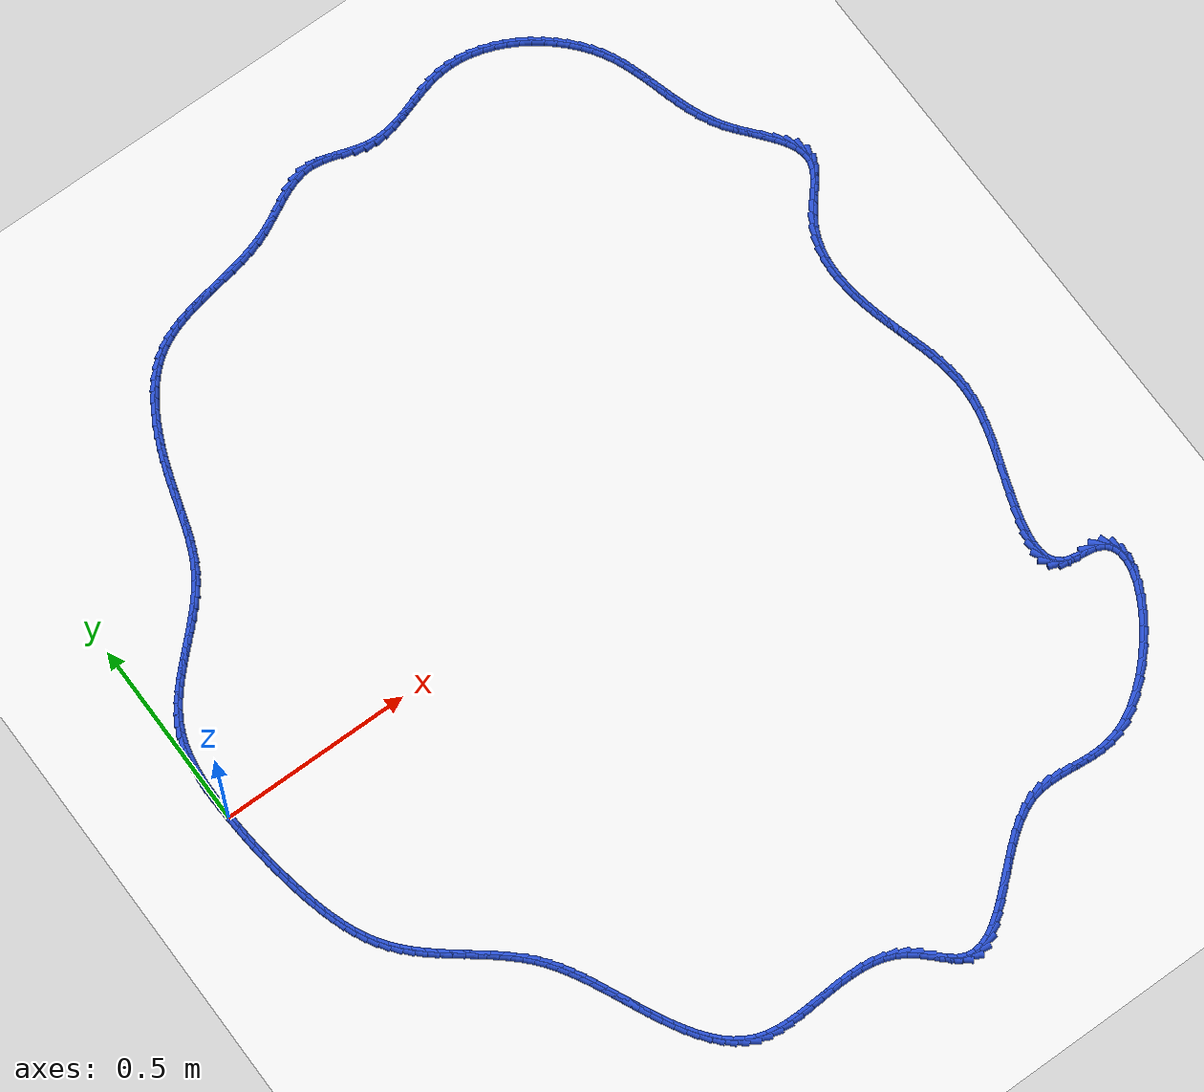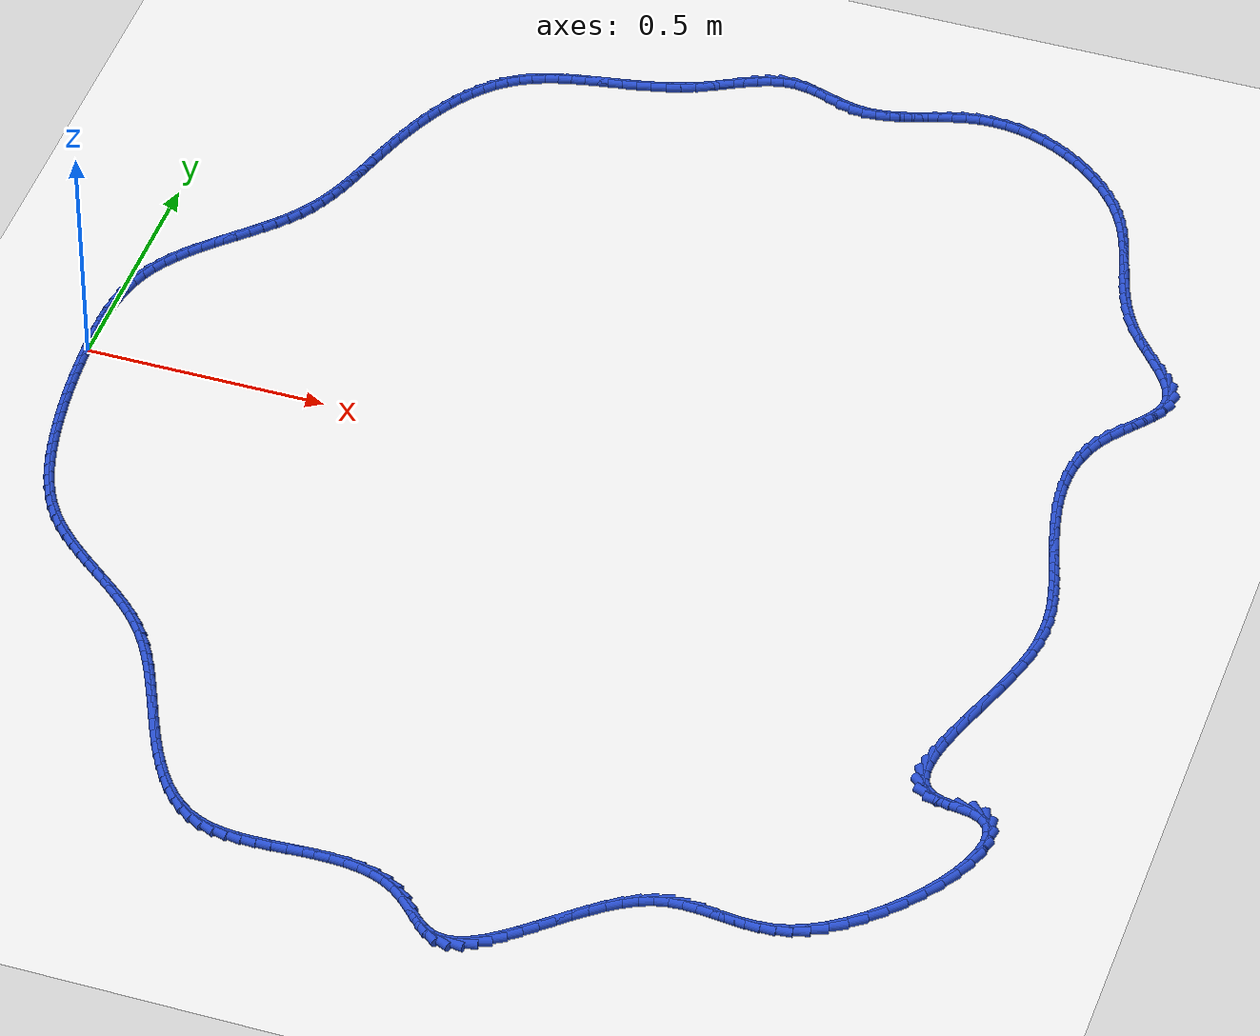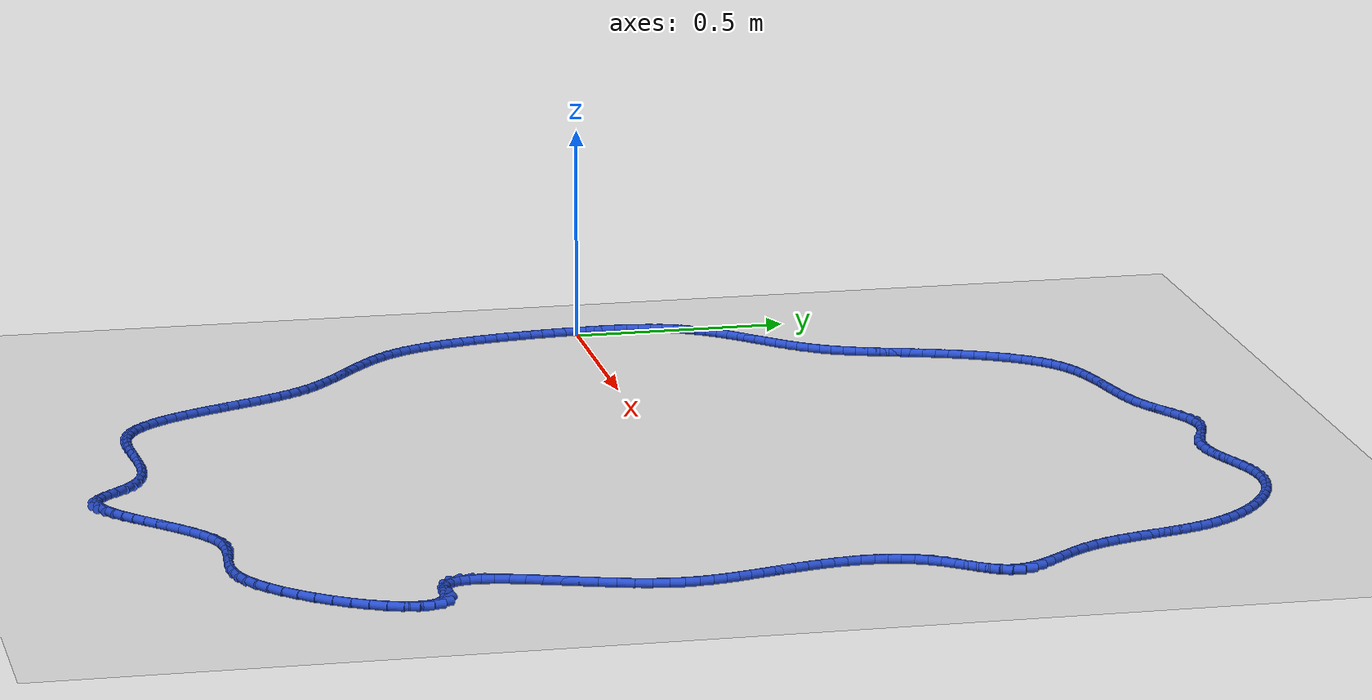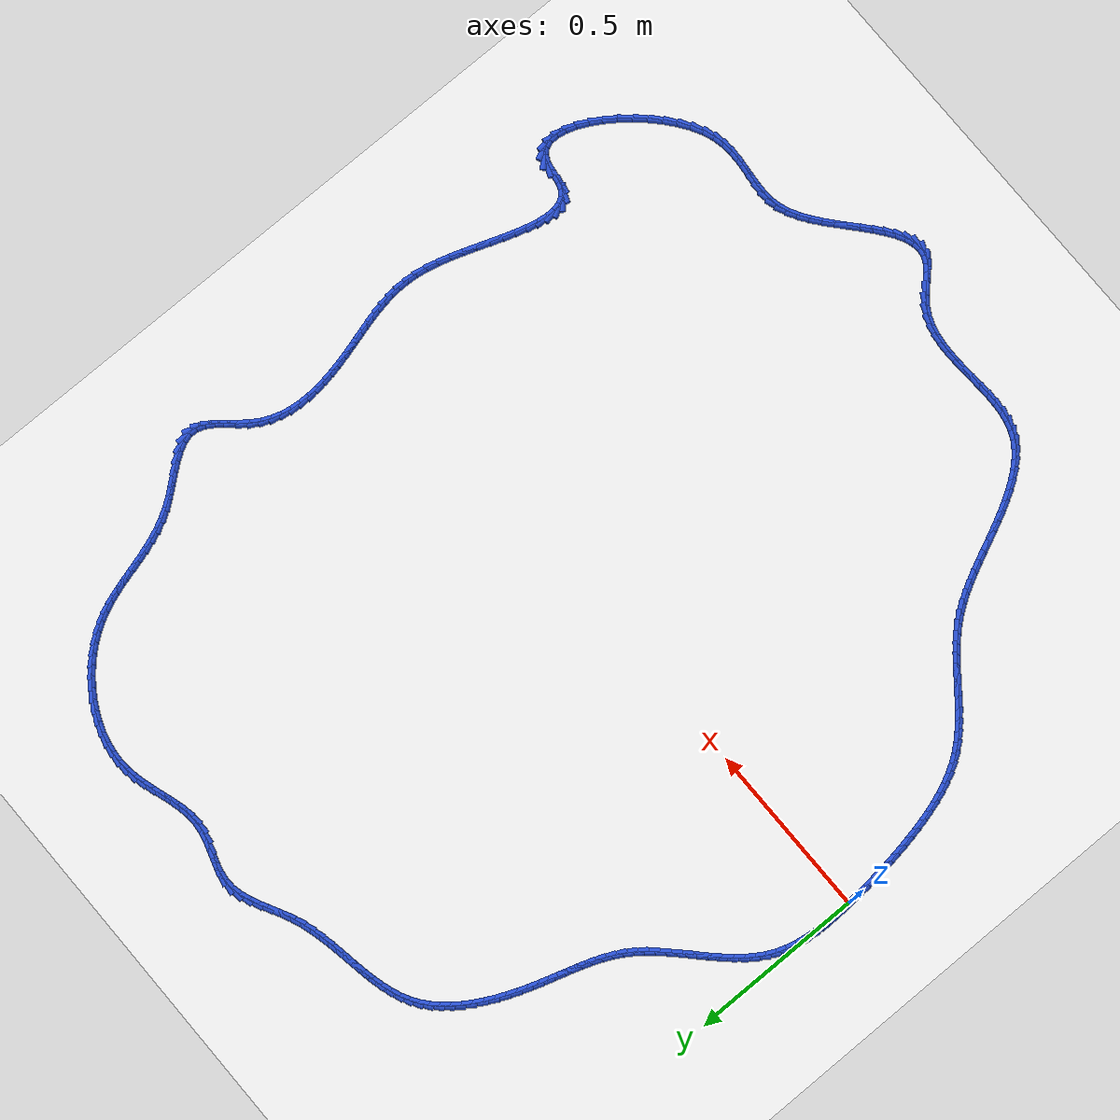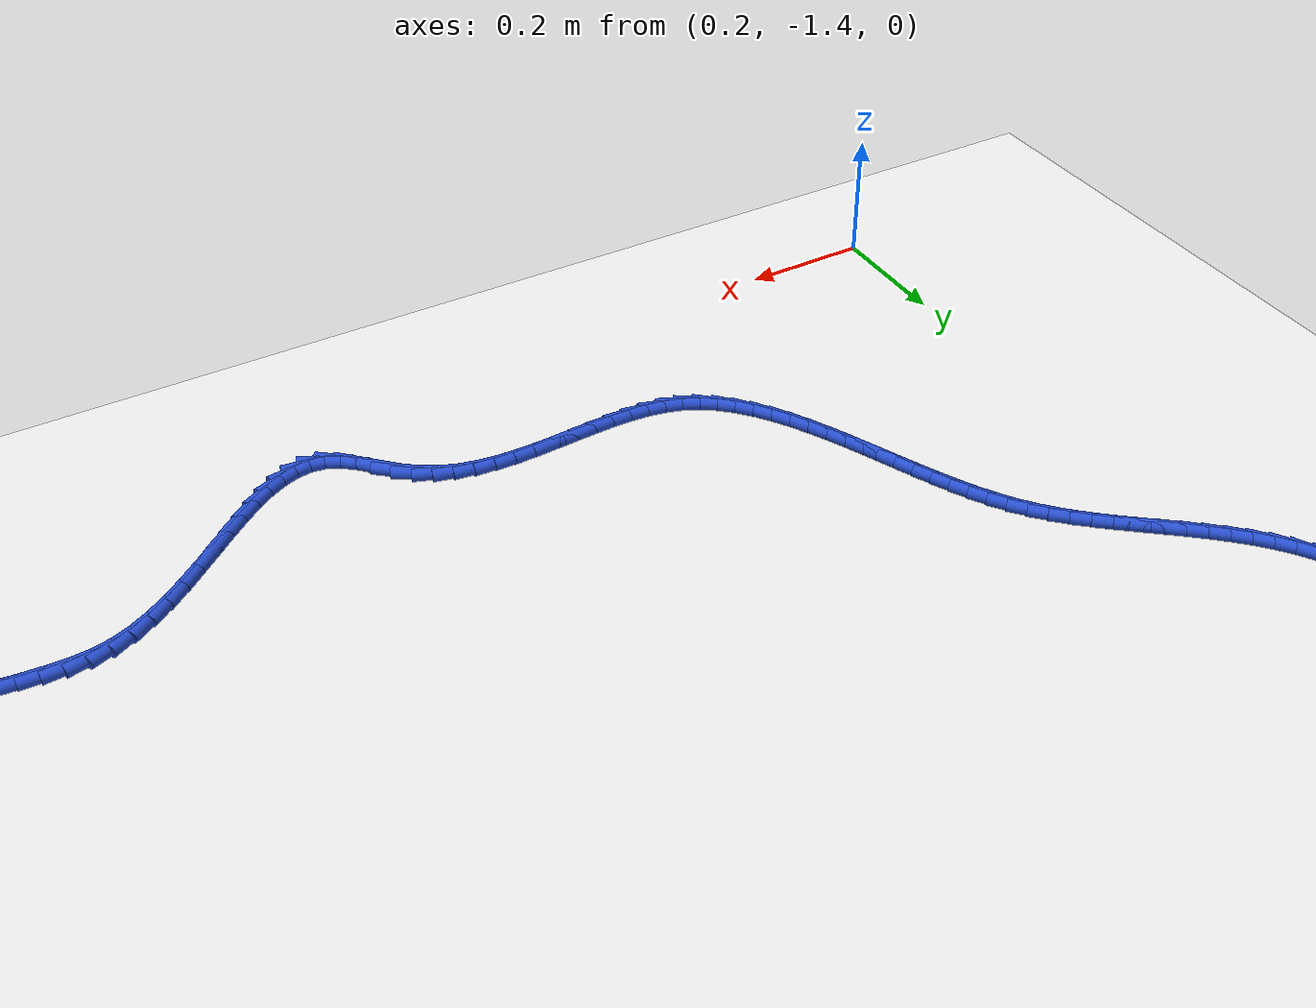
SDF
<sdf version="1.6">
 <world name="default">
  <light name="sun" type="directional">
   <pose>0 0 10 0 -0 0</pose>
   <diffuse>0.8 0.8 0.8 1</diffuse>
   <specular>0.2 0.2 0.2 1</specular>
   <attenuation>
    <range>1000</range>
    <constant>0.9</constant>
    <linear>0.01</linear>
    <quadratic>0.001</quadratic>
   </attenuation>
   <direction>-0.5 0.1 -0.9</direction>
  </light>
  <model name="ground_plane">
   <static>1</static>
   <link name="link">
    <collision name="collision">
     <geometry><plane><normal>0 0 1</normal><size>100 100</size></plane></geometry>
     <surface><friction><ode><mu>100</mu><mu2>50</mu2></ode></friction></surface>
    </collision>
    <visual name="visual">
     <cast_shadows>0</cast_shadows>
     <geometry><plane><normal>0 0 1</normal><size>100 100</size></plane></geometry>
     <material>
      <script><uri>file://media/materials/scripts/gazebo.material</uri><name>Gazebo/WhiteGlow</name></script>
     </material>
    </visual>
   </link>
  </model>
  <gravity>0 0 -9.8</gravity>
  <magnetic_field>6e-06 2.3e-05 -4.2e-05</magnetic_field>
  <atmosphere type="adiabatic"/>
  <physics name="default_physics" default="0" type="ode">
   <max_step_size>0.001</max_step_size>
   <real_time_factor>1</real_time_factor>
   <real_time_update_rate>1000</real_time_update_rate>
  </physics>
  <scene><ambient>0.4 0.4 0.4 1</ambient><background>0.7 0.7 0.7 1</background><shadows>1</shadows></scene>
  <spherical_coordinates>
   <surface_model>EARTH_WGS84</surface_model>
   <latitude_deg>0</latitude_deg>
   <longitude_deg>0</longitude_deg>
   <elevation>0</elevation>
   <heading_deg>0</heading_deg>
  </spherical_coordinates>
  <model name="line">
   <link name="link_0">
    <pose>-1.5016200088924236e-17 -4.163336342344337e-17 0.01 0 1.57 -1.5311288016451743</pose>
    <collision name="collision">
     <geometry><cylinder><radius>0.01</radius><length>0.08</length></cylinder></geometry>
    </collision>
    <visual name="visual">
     <material>
      <script><name>Gazebo/Blue</name><uri>file://media/materials/scripts/gazebo.material</uri></script>
     </material>
     <geometry><cylinder><radius>0.01</radius><length>0.08</length></cylinder></geometry>
    </visual>
   </link>
   <link name="link_1">
    <pose>-0.001174265937929834 0.02958717392838835 0.01 0 1.57 -1.5547759416217406</pose>
    <collision name="collision">
     <geometry><cylinder><radius>0.01</radius><length>0.08</length></cylinder></geometry>
    </collision>
    <visual name="visual">
     <material>
      <script><name>Gazebo/Blue</name><uri>file://media/materials/scripts/gazebo.material</uri></script>
     </material>
     <geometry><cylinder><radius>0.01</radius><length>0.08</length></cylinder></geometry>
    </visual>
   </link>
   <link name="link_2">
    <pose>-0.0016509662810044198 0.059340488538174856 0.01 0 1.57 1.554361322726253</pose>
    <collision name="collision">
     <geometry><cylinder><radius>0.01</radius><length>0.08</length></cylinder></geometry>
    </collision>
    <visual name="visual">
     <material>
      <script><name>Gazebo/Blue</name><uri>file://media/materials/scripts/gazebo.material</uri></script>
     </material>
     <geometry><cylinder><radius>0.01</radius><length>0.08</length></cylinder></geometry>
    </visual>
   </link>
   <link name="link_3">
    <pose>-0.0011624860198070212 0.08905975586146364 0.01 0 1.57 1.512484553610487</pose>
    <collision name="collision">
     <geometry><cylinder><radius>0.01</radius><length>0.08</length></cylinder></geometry>
    </collision>
    <visual name="visual">
     <material>
      <script><name>Gazebo/Blue</name><uri>file://media/materials/scripts/gazebo.material</uri></script>
     </material>
     <geometry><cylinder><radius>0.01</radius><length>0.08</length></cylinder></geometry>
    </visual>
   </link>
   <link name="link_4">
    <pose>0.0005587898550791126 0.11854478793035901 0.01 0 1.57 1.460348531937159</pose>
    <collision name="collision">
     <geometry><cylinder><radius>0.01</radius><length>0.08</length></cylinder></geometry>
    </collision>
    <visual name="visual">
     <material>
      <script><name>Gazebo/Blue</name><uri>file://media/materials/scripts/gazebo.material</uri></script>
     </material>
     <geometry><cylinder><radius>0.01</radius><length>0.08</length></cylinder></geometry>
    </visual>
   </link>
   <link name="link_5">
    <pose>0.0037804763530707333 0.14759539677696512 0.01 0 1.57 1.396973227693927</pose>
    <collision name="collision">
     <geometry><cylinder><radius>0.01</radius><length>0.08</length></cylinder></geometry>
    </collision>
    <visual name="visual">
     <material>
      <script><name>Gazebo/Blue</name><uri>file://media/materials/scripts/gazebo.material</uri></script>
     </material>
     <geometry><cylinder><radius>0.01</radius><length>0.08</length></cylinder></geometry>
    </visual>
   </link>
   <link name="link_6">
    <pose>0.00877018848358459 0.17601139443338618 0.01 0 1.57 1.321384697896744</pose>
    <collision name="collision">
     <geometry><cylinder><radius>0.01</radius><length>0.08</length></cylinder></geometry>
    </collision>
    <visual name="visual">
     <material>
      <script><name>Gazebo/Blue</name><uri>file://media/materials/scripts/gazebo.material</uri></script>
     </material>
     <geometry><cylinder><radius>0.01</radius><length>0.08</length></cylinder></geometry>
    </visual>
   </link>
   <link name="link_7">
    <pose>0.015795541256037438 0.20359259293172652 0.01 0 1.57 1.2328657916615506</pose>
    <collision name="collision">
     <geometry><cylinder><radius>0.01</radius><length>0.08</length></cylinder></geometry>
    </collision>
    <visual name="visual">
     <material>
      <script><name>Gazebo/Blue</name><uri>file://media/materials/scripts/gazebo.material</uri></script>
     </material>
     <geometry><cylinder><radius>0.01</radius><length>0.08</length></cylinder></geometry>
    </visual>
   </link>
   <link name="link_8">
    <pose>0.025124149679846018 0.23013880430409017 0.01 0 1.57 1.1324884987083297</pose>
    <collision name="collision">
     <geometry><cylinder><radius>0.01</radius><length>0.08</length></cylinder></geometry>
    </collision>
    <visual name="visual">
     <material>
      <script><name>Gazebo/Blue</name><uri>file://media/materials/scripts/gazebo.material</uri></script>
     </material>
     <geometry><cylinder><radius>0.01</radius><length>0.08</length></cylinder></geometry>
    </visual>
   </link>
   <link name="link_9">
    <pose>0.03699568034891773 0.25546662994324726 0.01 0 1.57 1.0359682667533752</pose>
    <collision name="collision">
     <geometry><cylinder><radius>0.01</radius><length>0.08</length></cylinder></geometry>
    </collision>
    <visual name="visual">
     <material>
      <script><name>Gazebo/Blue</name><uri>file://media/materials/scripts/gazebo.material</uri></script>
     </material>
     <geometry><cylinder><radius>0.01</radius><length>0.08</length></cylinder></geometry>
    </visual>
   </link>
   <link name="link_10">
    <pose>0.05129591208374488 0.27960526109204537 0.01 0 1.57 0.9547310295436591</pose>
    <collision name="collision">
     <geometry><cylinder><radius>0.01</radius><length>0.08</length></cylinder></geometry>
    </collision>
    <visual name="visual">
     <material>
      <script><name>Gazebo/Blue</name><uri>file://media/materials/scripts/gazebo.material</uri></script>
     </material>
     <geometry><cylinder><radius>0.01</radius><length>0.08</length></cylinder></geometry>
    </visual>
   </link>
   <link name="link_11">
    <pose>0.06766774557786781 0.3027297923798709 0.01 0 1.57 0.8892296630248957</pose>
    <collision name="collision">
     <geometry><cylinder><radius>0.01</radius><length>0.08</length></cylinder></geometry>
    </collision>
    <visual name="visual">
     <material>
      <script><name>Gazebo/Blue</name><uri>file://media/materials/scripts/gazebo.material</uri></script>
     </material>
     <geometry><cylinder><radius>0.01</radius><length>0.08</length></cylinder></geometry>
    </visual>
   </link>
   <link name="link_12">
    <pose>0.08574932593044152 0.32501817524884397 0.01 0 1.57 0.8389448791662363</pose>
    <collision name="collision">
     <geometry><cylinder><radius>0.01</radius><length>0.08</length></cylinder></geometry>
    </collision>
    <visual name="visual">
     <material>
      <script><name>Gazebo/Blue</name><uri>file://media/materials/scripts/gazebo.material</uri></script>
     </material>
     <geometry><cylinder><radius>0.01</radius><length>0.08</length></cylinder></geometry>
    </visual>
   </link>
   <link name="link_13">
    <pose>0.10517879824062105 0.34664836114108466 0.01 0 1.57 0.8030655910172035</pose>
    <collision name="collision">
     <geometry><cylinder><radius>0.01</radius><length>0.08</length></cylinder></geometry>
    </collision>
    <visual name="visual">
     <material>
      <script><name>Gazebo/Blue</name><uri>file://media/materials/scripts/gazebo.material</uri></script>
     </material>
     <geometry><cylinder><radius>0.01</radius><length>0.08</length></cylinder></geometry>
    </visual>
   </link>
   <link name="link_14">
    <pose>0.1255943076075614 0.3677983014987131 0.01 0 1.57 0.7808133909517982</pose>
    <collision name="collision">
     <geometry><cylinder><radius>0.01</radius><length>0.08</length></cylinder></geometry>
    </collision>
    <visual name="visual">
     <material>
      <script><name>Gazebo/Blue</name><uri>file://media/materials/scripts/gazebo.material</uri></script>
     </material>
     <geometry><cylinder><radius>0.01</radius><length>0.08</length></cylinder></geometry>
    </visual>
   </link>
   <link name="link_15">
    <pose>0.14663399913041758 0.3886459477638494 0.01 0 1.57 0.7716284037919562</pose>
    <collision name="collision">
     <geometry><cylinder><radius>0.01</radius><length>0.08</length></cylinder></geometry>
    </collision>
    <visual name="visual">
     <material>
      <script><name>Gazebo/Blue</name><uri>file://media/materials/scripts/gazebo.material</uri></script>
     </material>
     <geometry><cylinder><radius>0.01</radius><length>0.08</length></cylinder></geometry>
    </visual>
   </link>
   <link name="link_16">
    <pose>0.1679360179083446 0.40936925137861374 0.01 0 1.57 0.7752607123844468</pose>
    <collision name="collision">
     <geometry><cylinder><radius>0.01</radius><length>0.08</length></cylinder></geometry>
    </collision>
    <visual name="visual">
     <material>
      <script><name>Gazebo/Blue</name><uri>file://media/materials/scripts/gazebo.material</uri></script>
     </material>
     <geometry><cylinder><radius>0.01</radius><length>0.08</length></cylinder></geometry>
    </visual>
   </link>
   <link name="link_17">
    <pose>0.1891385090404975 0.43014616378512605 0.01 0 1.57 0.7918020695473644</pose>
    <collision name="collision">
     <geometry><cylinder><radius>0.01</radius><length>0.08</length></cylinder></geometry>
    </collision>
    <visual name="visual">
     <material>
      <script><name>Gazebo/Blue</name><uri>file://media/materials/scripts/gazebo.material</uri></script>
     </material>
     <geometry><cylinder><radius>0.01</radius><length>0.08</length></cylinder></geometry>
    </visual>
   </link>
   <link name="link_18">
    <pose>0.20987961762603127 0.45115463642550674 0.01 0 1.57 0.8216730903169859</pose>
    <collision name="collision">
     <geometry><cylinder><radius>0.01</radius><length>0.08</length></cylinder></geometry>
    </collision>
    <visual name="visual">
     <material>
      <script><name>Gazebo/Blue</name><uri>file://media/materials/scripts/gazebo.material</uri></script>
     </material>
     <geometry><cylinder><radius>0.01</radius><length>0.08</length></cylinder></geometry>
    </visual>
   </link>
   <link name="link_19">
    <pose>0.22979748876410092 0.4725726207418756 0.01 0 1.57 0.8655601133314805</pose>
    <collision name="collision">
     <geometry><cylinder><radius>0.01</radius><length>0.08</length></cylinder></geometry>
    </collision>
    <visual name="visual">
     <material>
      <script><name>Gazebo/Blue</name><uri>file://media/materials/scripts/gazebo.material</uri></script>
     </material>
     <geometry><cylinder><radius>0.01</radius><length>0.08</length></cylinder></geometry>
    </visual>
   </link>
   <link name="link_20">
    <pose>0.24853026755386146 0.49457806817635297 0.01 0 1.57 0.9242754758352315</pose>
    <collision name="collision">
     <geometry><cylinder><radius>0.01</radius><length>0.08</length></cylinder></geometry>
    </collision>
    <visual name="visual">
     <material>
      <script><name>Gazebo/Blue</name><uri>file://media/materials/scripts/gazebo.material</uri></script>
     </material>
     <geometry><cylinder><radius>0.01</radius><length>0.08</length></cylinder></geometry>
    </visual>
   </link>
   <link name="link_21">
    <pose>0.26571609909446803 0.517348930171059 0.01 0 1.57 0.9979697683734182</pose>
    <collision name="collision">
     <geometry><cylinder><radius>0.01</radius><length>0.08</length></cylinder></geometry>
    </collision>
    <visual name="visual">
     <material>
      <script><name>Gazebo/Blue</name><uri>file://media/materials/scripts/gazebo.material</uri></script>
     </material>
     <geometry><cylinder><radius>0.01</radius><length>0.08</length></cylinder></geometry>
    </visual>
   </link>
   <link name="link_22">
    <pose>0.2810072242214734 0.5410574379976409 0.01 0 1.57 1.0741629369633323</pose>
    <collision name="collision">
     <geometry><cylinder><radius>0.01</radius><length>0.08</length></cylinder></geometry>
    </collision>
    <visual name="visual">
     <material>
      <script><name>Gazebo/Blue</name><uri>file://media/materials/scripts/gazebo.material</uri></script>
     </material>
     <geometry><cylinder><radius>0.01</radius><length>0.08</length></cylinder></geometry>
    </visual>
   </link>
   <link name="link_23">
    <pose>0.2943849162970617 0.565742298712326 0.01 0 1.57 1.1391013435100492</pose>
    <collision name="collision">
     <geometry><cylinder><radius>0.01</radius><length>0.08</length></cylinder></geometry>
    </collision>
    <visual name="visual">
     <material>
      <script><name>Gazebo/Blue</name><uri>file://media/materials/scripts/gazebo.material</uri></script>
     </material>
     <geometry><cylinder><radius>0.01</radius><length>0.08</length></cylinder></geometry>
    </visual>
   </link>
   <link name="link_24">
    <pose>0.3061621874583513 0.5913075969371968 0.01 0 1.57 1.1913720280829216</pose>
    <collision name="collision">
     <geometry><cylinder><radius>0.01</radius><length>0.08</length></cylinder></geometry>
    </collision>
    <visual name="visual">
     <material>
      <script><name>Gazebo/Blue</name><uri>file://media/materials/scripts/gazebo.material</uri></script>
     </material>
     <geometry><cylinder><radius>0.01</radius><length>0.08</length></cylinder></geometry>
    </visual>
   </link>
   <link name="link_25">
    <pose>0.3166666868399034 0.6176514774754983 0.01 0 1.57 1.2307571406425042</pose>
    <collision name="collision">
     <geometry><cylinder><radius>0.01</radius><length>0.08</length></cylinder></geometry>
    </collision>
    <visual name="visual">
     <material>
      <script><name>Gazebo/Blue</name><uri>file://media/materials/scripts/gazebo.material</uri></script>
     </material>
     <geometry><cylinder><radius>0.01</radius><length>0.08</length></cylinder></geometry>
    </visual>
   </link>
   <link name="link_26">
    <pose>0.32622606357627965 0.6446720851304766 0.01 0 1.57 1.2574374189947841</pose>
    <collision name="collision">
     <geometry><cylinder><radius>0.01</radius><length>0.08</length></cylinder></geometry>
    </collision>
    <visual name="visual">
     <material>
      <script><name>Gazebo/Blue</name><uri>file://media/materials/scripts/gazebo.material</uri></script>
     </material>
     <geometry><cylinder><radius>0.01</radius><length>0.08</length></cylinder></geometry>
    </visual>
   </link>
   <link name="link_27">
    <pose>0.3351679668020412 0.6722675647053767 0.01 0 1.57 1.2717891587557226</pose>
    <collision name="collision">
     <geometry><cylinder><radius>0.01</radius><length>0.08</length></cylinder></geometry>
    </collision>
    <visual name="visual">
     <material>
      <script><name>Gazebo/Blue</name><uri>file://media/materials/scripts/gazebo.material</uri></script>
     </material>
     <geometry><cylinder><radius>0.01</radius><length>0.08</length></cylinder></geometry>
    </visual>
   </link>
   <link name="link_28">
    <pose>0.3438200456517494 0.7003360610034441 0.01 0 1.57 1.2742502552433834</pose>
    <collision name="collision">
     <geometry><cylinder><radius>0.01</radius><length>0.08</length></cylinder></geometry>
    </collision>
    <visual name="visual">
     <material>
      <script><name>Gazebo/Blue</name><uri>file://media/materials/scripts/gazebo.material</uri></script>
     </material>
     <geometry><cylinder><radius>0.01</radius><length>0.08</length></cylinder></geometry>
    </visual>
   </link>
   <link name="link_29">
    <pose>0.35250994925996565 0.7287757188279242 0.01 0 1.57 1.2652535866409103</pose>
    <collision name="collision">
     <geometry><cylinder><radius>0.01</radius><length>0.08</length></cylinder></geometry>
    </collision>
    <visual name="visual">
     <material>
      <script><name>Gazebo/Blue</name><uri>file://media/materials/scripts/gazebo.material</uri></script>
     </material>
     <geometry><cylinder><radius>0.01</radius><length>0.08</length></cylinder></geometry>
    </visual>
   </link>
   <link name="link_30">
    <pose>0.3615653267612513 0.7574846829820628 0.01 0 1.57 1.245582630229372</pose>
    <collision name="collision">
     <geometry><cylinder><radius>0.01</radius><length>0.08</length></cylinder></geometry>
    </collision>
    <visual name="visual">
     <material>
      <script><name>Gazebo/Blue</name><uri>file://media/materials/scripts/gazebo.material</uri></script>
     </material>
     <geometry><cylinder><radius>0.01</radius><length>0.08</length></cylinder></geometry>
    </visual>
   </link>
   <link name="link_31">
    <pose>0.37129936071062236 0.786353146374145 0.01 0 1.57 1.2193768277337889</pose>
    <collision name="collision">
     <geometry><cylinder><radius>0.01</radius><length>0.08</length></cylinder></geometry>
    </collision>
    <visual name="visual">
     <material>
      <script><name>Gazebo/Blue</name><uri>file://media/materials/scripts/gazebo.material</uri></script>
     </material>
     <geometry><cylinder><radius>0.01</radius><length>0.08</length></cylinder></geometry>
    </visual>
   </link>
   <link name="link_32">
    <pose>0.38187071407639517 0.8151863665952443 0.01 0 1.57 1.1886893198190853</pose>
    <collision name="collision">
     <geometry><cylinder><radius>0.01</radius><length>0.08</length></cylinder></geometry>
    </collision>
    <visual name="visual">
     <material>
      <script><name>Gazebo/Blue</name><uri>file://media/materials/scripts/gazebo.material</uri></script>
     </material>
     <geometry><cylinder><radius>0.01</radius><length>0.08</length></cylinder></geometry>
    </visual>
   </link>
   <link name="link_33">
    <pose>0.39334448231849006 0.8437381696595311 0.01 0 1.57 1.1530164887138044</pose>
    <collision name="collision">
     <geometry><cylinder><radius>0.01</radius><length>0.08</length></cylinder></geometry>
    </collision>
    <visual name="visual">
     <material>
      <script><name>Gazebo/Blue</name><uri>file://media/materials/scripts/gazebo.material</uri></script>
     </material>
     <geometry><cylinder><radius>0.01</radius><length>0.08</length></cylinder></geometry>
    </visual>
   </link>
   <link name="link_34">
    <pose>0.4057844547920023 0.8717616636500055 0.01 0 1.57 1.1116856371248138</pose>
    <collision name="collision">
     <geometry><cylinder><radius>0.01</radius><length>0.08</length></cylinder></geometry>
    </collision>
    <visual name="visual">
     <material>
      <script><name>Gazebo/Blue</name><uri>file://media/materials/scripts/gazebo.material</uri></script>
     </material>
     <geometry><cylinder><radius>0.01</radius><length>0.08</length></cylinder></geometry>
    </visual>
   </link>
   <link name="link_35">
    <pose>0.41925442085202713 0.8990099566496682 0.01 0 1.57 1.06388321531544</pose>
    <collision name="collision">
     <geometry><cylinder><radius>0.01</radius><length>0.08</length></cylinder></geometry>
    </collision>
    <visual name="visual">
     <material>
      <script><name>Gazebo/Blue</name><uri>file://media/materials/scripts/gazebo.material</uri></script>
     </material>
     <geometry><cylinder><radius>0.01</radius><length>0.08</length></cylinder></geometry>
    </visual>
   </link>
   <link name="link_36">
    <pose>0.4338181698536592 0.9252361567415188 0.01 0 1.57 1.0086590446963872</pose>
    <collision name="collision">
     <geometry><cylinder><radius>0.01</radius><length>0.08</length></cylinder></geometry>
    </collision>
    <visual name="visual">
     <material>
      <script><name>Gazebo/Blue</name><uri>file://media/materials/scripts/gazebo.material</uri></script>
     </material>
     <geometry><cylinder><radius>0.01</radius><length>0.08</length></cylinder></geometry>
    </visual>
   </link>
   <link name="link_37">
    <pose>0.4495394911519939 0.9501933720085578 0.01 0 1.57 0.9449517527124083</pose>
    <collision name="collision">
     <geometry><cylinder><radius>0.01</radius><length>0.08</length></cylinder></geometry>
    </collision>
    <visual name="visual">
     <material>
      <script><name>Gazebo/Blue</name><uri>file://media/materials/scripts/gazebo.material</uri></script>
     </material>
     <geometry><cylinder><radius>0.01</radius><length>0.08</length></cylinder></geometry>
    </visual>
   </link>
   <link name="link_38">
    <pose>0.46648217410212645 0.973634710533786 0.01 0 1.57 0.8716543368457267</pose>
    <collision name="collision">
     <geometry><cylinder><radius>0.01</radius><length>0.08</length></cylinder></geometry>
    </collision>
    <visual name="visual">
     <material>
      <script><name>Gazebo/Blue</name><uri>file://media/materials/scripts/gazebo.material</uri></script>
     </material>
     <geometry><cylinder><radius>0.01</radius><length>0.08</length></cylinder></geometry>
    </visual>
   </link>
   <link name="link_39">
    <pose>0.4847100080591516 0.995313280400203 0.01 0 1.57 0.7877458050704825</pose>
    <collision name="collision">
     <geometry><cylinder><radius>0.01</radius><length>0.08</length></cylinder></geometry>
    </collision>
    <visual name="visual">
     <material>
      <script><name>Gazebo/Blue</name><uri>file://media/materials/scripts/gazebo.material</uri></script>
     </material>
     <geometry><cylinder><radius>0.01</radius><length>0.08</length></cylinder></geometry>
    </visual>
   </link>
   <link name="link_40">
    <pose>0.5042867823781646 1.0149821896908096 0.01 0 1.57 0.6925158289524688</pose>
    <collision name="collision">
     <geometry><cylinder><radius>0.01</radius><length>0.08</length></cylinder></geometry>
    </collision>
    <visual name="visual">
     <material>
      <script><name>Gazebo/Blue</name><uri>file://media/materials/scripts/gazebo.material</uri></script>
     </material>
     <geometry><cylinder><radius>0.01</radius><length>0.08</length></cylinder></geometry>
    </visual>
   </link>
   <link name="link_41">
    <pose>0.5252762864142605 1.0323945464886053 0.01 0 1.57 0.5861597651782825</pose>
    <collision name="collision">
     <geometry><cylinder><radius>0.01</radius><length>0.08</length></cylinder></geometry>
    </collision>
    <visual name="visual">
     <material>
      <script><name>Gazebo/Blue</name><uri>file://media/materials/scripts/gazebo.material</uri></script>
     </material>
     <geometry><cylinder><radius>0.01</radius><length>0.08</length></cylinder></geometry>
    </visual>
   </link>
   <link name="link_42">
    <pose>0.5477396904743252 1.047310427666039 0.01 0 1.57 0.47980976713616075</pose>
    <collision name="collision">
     <geometry><cylinder><radius>0.01</radius><length>0.08</length></cylinder></geometry>
    </collision>
    <visual name="visual">
     <material>
      <script><name>Gazebo/Blue</name><uri>file://media/materials/scripts/gazebo.material</uri></script>
     </material>
     <geometry><cylinder><radius>0.01</radius><length>0.08</length></cylinder></geometry>
    </visual>
   </link>
   <link name="link_43">
    <pose>0.5716411626215503 1.0597480146275238 0.01 0 1.57 0.38847029238546765</pose>
    <collision name="collision">
     <geometry><cylinder><radius>0.01</radius><length>0.08</length></cylinder></geometry>
    </collision>
    <visual name="visual">
     <material>
      <script><name>Gazebo/Blue</name><uri>file://media/materials/scripts/gazebo.material</uri></script>
     </material>
     <geometry><cylinder><radius>0.01</radius><length>0.08</length></cylinder></geometry>
    </visual>
   </link>
   <link name="link_44">
    <pose>0.5968215774885719 1.0700535491601595 0.01 0 1.57 0.31409264425457817</pose>
    <collision name="collision">
     <geometry><cylinder><radius>0.01</radius><length>0.08</length></cylinder></geometry>
    </collision>
    <visual name="visual">
     <material>
      <script><name>Gazebo/Blue</name><uri>file://media/materials/scripts/gazebo.material</uri></script>
     </material>
     <geometry><cylinder><radius>0.01</radius><length>0.08</length></cylinder></geometry>
    </visual>
   </link>
   <link name="link_45">
    <pose>0.6231138374282352 1.078594485772173 0.01 0 1.57 0.25650493725613693</pose>
    <collision name="collision">
     <geometry><cylinder><radius>0.01</radius><length>0.08</length></cylinder></geometry>
    </collision>
    <visual name="visual">
     <material>
      <script><name>Gazebo/Blue</name><uri>file://media/materials/scripts/gazebo.material</uri></script>
     </material>
     <geometry><cylinder><radius>0.01</radius><length>0.08</length></cylinder></geometry>
    </visual>
   </link>
   <link name="link_46">
    <pose>0.6503508447933862 1.0857382789717926 0.01 0 1.57 0.21487725893842557</pose>
    <collision name="collision">
     <geometry><cylinder><radius>0.01</radius><length>0.08</length></cylinder></geometry>
    </collision>
    <visual name="visual">
     <material>
      <script><name>Gazebo/Blue</name><uri>file://media/materials/scripts/gazebo.material</uri></script>
     </material>
     <geometry><cylinder><radius>0.01</radius><length>0.08</length></cylinder></geometry>
    </visual>
   </link>
   <link name="link_47">
    <pose>0.6783655019368693 1.0918523832672455 0.01 0 1.57 0.1882029332642791</pose>
    <collision name="collision">
     <geometry><cylinder><radius>0.01</radius><length>0.08</length></cylinder></geometry>
    </collision>
    <visual name="visual">
     <material>
      <script><name>Gazebo/Blue</name><uri>file://media/materials/scripts/gazebo.material</uri></script>
     </material>
     <geometry><cylinder><radius>0.01</radius><length>0.08</length></cylinder></geometry>
    </visual>
   </link>
   <link name="link_48">
    <pose>0.7069907112115298 1.0973042531667592 0.01 0 1.57 0.17558370539319626</pose>
    <collision name="collision">
     <geometry><cylinder><radius>0.01</radius><length>0.08</length></cylinder></geometry>
    </collision>
    <visual name="visual">
     <material>
      <script><name>Gazebo/Blue</name><uri>file://media/materials/scripts/gazebo.material</uri></script>
     </material>
     <geometry><cylinder><radius>0.01</radius><length>0.08</length></cylinder></geometry>
    </visual>
   </link>
   <link name="link_49">
    <pose>0.7360593749702127 1.102461343178561 0.01 0 1.57 0.17636480083615735</pose>
    <collision name="collision">
     <geometry><cylinder><radius>0.01</radius><length>0.08</length></cylinder></geometry>
    </collision>
    <visual name="visual">
     <material>
      <script><name>Gazebo/Blue</name><uri>file://media/materials/scripts/gazebo.material</uri></script>
     </material>
     <geometry><cylinder><radius>0.01</radius><length>0.08</length></cylinder></geometry>
    </visual>
   </link>
   <link name="link_50">
    <pose>0.7654043955657637 1.1076911078108789 0.01 0 1.57 0.19017192688713616</pose>
    <collision name="collision">
     <geometry><cylinder><radius>0.01</radius><length>0.08</length></cylinder></geometry>
    </collision>
    <visual name="visual">
     <material>
      <script><name>Gazebo/Blue</name><uri>file://media/materials/scripts/gazebo.material</uri></script>
     </material>
     <geometry><cylinder><radius>0.01</radius><length>0.08</length></cylinder></geometry>
    </visual>
   </link>
   <link name="link_51">
    <pose>0.7948586753510278 1.1133610015719406 0.01 0 1.57 0.21688319954885313</pose>
    <collision name="collision">
     <geometry><cylinder><radius>0.01</radius><length>0.08</length></cylinder></geometry>
    </collision>
    <visual name="visual">
     <material>
      <script><name>Gazebo/Blue</name><uri>file://media/materials/scripts/gazebo.material</uri></script>
     </material>
     <geometry><cylinder><radius>0.01</radius><length>0.08</length></cylinder></geometry>
    </visual>
   </link>
   <link name="link_52">
    <pose>0.8242551166788498 1.1198384789699727 0.01 0 1.57 0.25654782590523983</pose>
    <collision name="collision">
     <geometry><cylinder><radius>0.01</radius><length>0.08</length></cylinder></geometry>
    </collision>
    <visual name="visual">
     <material>
      <script><name>Gazebo/Blue</name><uri>file://media/materials/scripts/gazebo.material</uri></script>
     </material>
     <geometry><cylinder><radius>0.01</radius><length>0.08</length></cylinder></geometry>
    </visual>
   </link>
   <link name="link_53">
    <pose>0.8534266219020752 1.1274909945132037 0.01 0 1.57 0.3092482843550311</pose>
    <collision name="collision">
     <geometry><cylinder><radius>0.01</radius><length>0.08</length></cylinder></geometry>
    </collision>
    <visual name="visual">
     <material>
      <script><name>Gazebo/Blue</name><uri>file://media/materials/scripts/gazebo.material</uri></script>
     </material>
     <geometry><cylinder><radius>0.01</radius><length>0.08</length></cylinder></geometry>
    </visual>
   </link>
   <link name="link_54">
    <pose>0.8822060933735488 1.1366860027098602 0.01 0 1.57 0.3748933982670792</pose>
    <collision name="collision">
     <geometry><cylinder><radius>0.01</radius><length>0.08</length></cylinder></geometry>
    </collision>
    <visual name="visual">
     <material>
      <script><name>Gazebo/Blue</name><uri>file://media/materials/scripts/gazebo.material</uri></script>
     </material>
     <geometry><cylinder><radius>0.01</radius><length>0.08</length></cylinder></geometry>
    </visual>
   </link>
   <link name="link_55">
    <pose>0.910426465148928 1.1477908167104476 0.01 0 1.57 0.4423941153000885</pose>
    <collision name="collision">
     <geometry><cylinder><radius>0.01</radius><length>0.08</length></cylinder></geometry>
    </collision>
    <visual name="visual">
     <material>
      <script><name>Gazebo/Blue</name><uri>file://media/materials/scripts/gazebo.material</uri></script>
     </material>
     <geometry><cylinder><radius>0.01</radius><length>0.08</length></cylinder></geometry>
    </visual>
   </link>
   <link name="link_56">
    <pose>0.937993187969242 1.1608494094594837 0.01 0 1.57 0.47893486279791403</pose>
    <collision name="collision">
     <geometry><cylinder><radius>0.01</radius><length>0.08</length></cylinder></geometry>
    </collision>
    <visual name="visual">
     <material>
      <script><name>Gazebo/Blue</name><uri>file://media/materials/scripts/gazebo.material</uri></script>
     </material>
     <geometry><cylinder><radius>0.01</radius><length>0.08</length></cylinder></geometry>
    </visual>
   </link>
   <link name="link_57">
    <pose>0.9650388309628827 1.1748930696375326 0.01 0 1.57 0.47885646915655644</pose>
    <collision name="collision">
     <geometry><cylinder><radius>0.01</radius><length>0.08</length></cylinder></geometry>
    </collision>
    <visual name="visual">
     <material>
      <script><name>Gazebo/Blue</name><uri>file://media/materials/scripts/gazebo.material</uri></script>
     </material>
     <geometry><cylinder><radius>0.01</radius><length>0.08</length></cylinder></geometry>
    </visual>
   </link>
   <link name="link_58">
    <pose>0.9917403076815139 1.1887553612928003 0.01 0 1.57 0.4406997888402698</pose>
    <collision name="collision">
     <geometry><cylinder><radius>0.01</radius><length>0.08</length></cylinder></geometry>
    </collision>
    <visual name="visual">
     <material>
      <script><name>Gazebo/Blue</name><uri>file://media/materials/scripts/gazebo.material</uri></script>
     </material>
     <geometry><cylinder><radius>0.01</radius><length>0.08</length></cylinder></geometry>
    </visual>
   </link>
   <link name="link_59">
    <pose>1.0182745316768 1.2012698484734925 0.01 0 1.57 0.3602986937750224</pose>
    <collision name="collision">
     <geometry><cylinder><radius>0.01</radius><length>0.08</length></cylinder></geometry>
    </collision>
    <visual name="visual">
     <material>
      <script><name>Gazebo/Blue</name><uri>file://media/materials/scripts/gazebo.material</uri></script>
     </material>
     <geometry><cylinder><radius>0.01</radius><length>0.08</length></cylinder></geometry>
    </visual>
   </link>
   <link name="link_60">
    <pose>1.0448184165004042 1.2112700952278148 0.01 0 1.57 0.23215563186837848</pose>
    <collision name="collision">
     <geometry><cylinder><radius>0.01</radius><length>0.08</length></cylinder></geometry>
    </collision>
    <visual name="visual">
     <material>
      <script><name>Gazebo/Blue</name><uri>file://media/materials/scripts/gazebo.material</uri></script>
     </material>
     <geometry><cylinder><radius>0.01</radius><length>0.08</length></cylinder></geometry>
    </visual>
   </link>
   <link name="link_61">
    <pose>1.0715488757039915 1.217589665603973 0.01 0 1.57 0.05435777274545825</pose>
    <collision name="collision">
     <geometry><cylinder><radius>0.01</radius><length>0.08</length></cylinder></geometry>
    </collision>
    <visual name="visual">
     <material>
      <script><name>Gazebo/Blue</name><uri>file://media/materials/scripts/gazebo.material</uri></script>
     </material>
     <geometry><cylinder><radius>0.01</radius><length>0.08</length></cylinder></geometry>
    </visual>
   </link>
   <link name="link_62">
    <pose>1.0986426525846236 1.2190638752387835 0.01 0 1.57 -0.13552404900785117</pose>
    <collision name="collision">
     <geometry><cylinder><radius>0.01</radius><length>0.08</length></cylinder></geometry>
    </collision>
    <visual name="visual">
     <material>
      <script><name>Gazebo/Blue</name><uri>file://media/materials/scripts/gazebo.material</uri></script>
     </material>
     <geometry><cylinder><radius>0.01</radius><length>0.08</length></cylinder></geometry>
    </visual>
   </link>
   <link name="link_63">
    <pose>1.1262008687773615 1.2153060395453452 0.01 0 1.57 -0.25827537090885283</pose>
    <collision name="collision">
     <geometry><cylinder><radius>0.01</radius><length>0.08</length></cylinder></geometry>
    </collision>
    <visual name="visual">
     <material>
      <script><name>Gazebo/Blue</name><uri>file://media/materials/scripts/gazebo.material</uri></script>
     </material>
     <geometry><cylinder><radius>0.01</radius><length>0.08</length></cylinder></geometry>
    </visual>
   </link>
   <link name="link_64">
    <pose>1.1541304150347456 1.2079277318319839 0.01 0 1.57 -0.31144655986879355</pose>
    <collision name="collision">
     <geometry><cylinder><radius>0.01</radius><length>0.08</length></cylinder></geometry>
    </collision>
    <visual name="visual">
     <material>
      <script><name>Gazebo/Blue</name><uri>file://media/materials/scripts/gazebo.material</uri></script>
     </material>
     <geometry><cylinder><radius>0.01</radius><length>0.08</length></cylinder></geometry>
    </visual>
   </link>
   <link name="link_65">
    <pose>1.1823074308834507 1.1988568956931442 0.01 0 1.57 -0.3026104360789553</pose>
    <collision name="collision">
     <geometry><cylinder><radius>0.01</radius><length>0.08</length></cylinder></geometry>
    </collision>
    <visual name="visual">
     <material>
      <script><name>Gazebo/Blue</name><uri>file://media/materials/scripts/gazebo.material</uri></script>
     </material>
     <geometry><cylinder><radius>0.01</radius><length>0.08</length></cylinder></geometry>
    </visual>
   </link>
   <link name="link_66">
    <pose>1.2106080558501522 1.190021474723272 0.01 0 1.57 -0.23153092995129998</pose>
    <collision name="collision">
     <geometry><cylinder><radius>0.01</radius><length>0.08</length></cylinder></geometry>
    </collision>
    <visual name="visual">
     <material>
      <script><name>Gazebo/Blue</name><uri>file://media/materials/scripts/gazebo.material</uri></script>
     </material>
     <geometry><cylinder><radius>0.01</radius><length>0.08</length></cylinder></geometry>
    </visual>
   </link>
   <link name="link_67">
    <pose>1.2389084294615245 1.183349412516813 0.01 0 1.57 -0.09519659210859714</pose>
    <collision name="collision">
     <geometry><cylinder><radius>0.01</radius><length>0.08</length></cylinder></geometry>
    </collision>
    <visual name="visual">
     <material>
      <script><name>Gazebo/Blue</name><uri>file://media/materials/scripts/gazebo.material</uri></script>
     </material>
     <geometry><cylinder><radius>0.01</radius><length>0.08</length></cylinder></geometry>
    </visual>
   </link>
   <link name="link_68">
    <pose>1.2670918527298065 1.180658312485066 0.01 0 1.57 0.05476848052000872</pose>
    <collision name="collision">
     <geometry><cylinder><radius>0.01</radius><length>0.08</length></cylinder></geometry>
    </collision>
    <visual name="visual">
     <material>
      <script><name>Gazebo/Blue</name><uri>file://media/materials/scripts/gazebo.material</uri></script>
     </material>
     <geometry><cylinder><radius>0.01</radius><length>0.08</length></cylinder></geometry>
    </visual>
   </link>
   <link name="link_69">
    <pose>1.295143498310333 1.1821961964691683 0.01 0 1.57 0.1715222598980427</pose>
    <collision name="collision">
     <geometry><cylinder><radius>0.01</radius><length>0.08</length></cylinder></geometry>
    </collision>
    <visual name="visual">
     <material>
      <script><name>Gazebo/Blue</name><uri>file://media/materials/scripts/gazebo.material</uri></script>
     </material>
     <geometry><cylinder><radius>0.01</radius><length>0.08</length></cylinder></geometry>
    </visual>
   </link>
   <link name="link_70">
    <pose>1.3231243416039968 1.1870431598021762 0.01 0 1.57 0.25220375406498796</pose>
    <collision name="collision">
     <geometry><cylinder><radius>0.01</radius><length>0.08</length></cylinder></geometry>
    </collision>
    <visual name="visual">
     <material>
      <script><name>Gazebo/Blue</name><uri>file://media/materials/scripts/gazebo.material</uri></script>
     </material>
     <geometry><cylinder><radius>0.01</radius><length>0.08</length></cylinder></geometry>
    </visual>
   </link>
   <link name="link_71">
    <pose>1.3510971625064938 1.1942514951656618 0.01 0 1.57 0.2984379741879921</pose>
    <collision name="collision">
     <geometry><cylinder><radius>0.01</radius><length>0.08</length></cylinder></geometry>
    </collision>
    <visual name="visual">
     <material>
      <script><name>Gazebo/Blue</name><uri>file://media/materials/scripts/gazebo.material</uri></script>
     </material>
     <geometry><cylinder><radius>0.01</radius><length>0.08</length></cylinder></geometry>
    </visual>
   </link>
   <link name="link_72">
    <pose>1.3791247409135214 1.202873495241198 0.01 0 1.57 0.3123281187690076</pose>
    <collision name="collision">
     <geometry><cylinder><radius>0.01</radius><length>0.08</length></cylinder></geometry>
    </collision>
    <visual name="visual">
     <material>
      <script><name>Gazebo/Blue</name><uri>file://media/materials/scripts/gazebo.material</uri></script>
     </material>
     <geometry><cylinder><radius>0.01</radius><length>0.08</length></cylinder></geometry>
    </visual>
   </link>
   <link name="link_73">
    <pose>1.4072698567207762 1.2119614527103575 0.01 0 1.57 0.29496978924033357</pose>
    <collision name="collision">
     <geometry><cylinder><radius>0.01</radius><length>0.08</length></cylinder></geometry>
    </collision>
    <visual name="visual">
     <material>
      <script><name>Gazebo/Blue</name><uri>file://media/materials/scripts/gazebo.material</uri></script>
     </material>
     <geometry><cylinder><radius>0.01</radius><length>0.08</length></cylinder></geometry>
    </visual>
   </link>
   <link name="link_74">
    <pose>1.435595289823955 1.2205676602547129 0.01 0 1.57 0.2461188019172089</pose>
    <collision name="collision">
     <geometry><cylinder><radius>0.01</radius><length>0.08</length></cylinder></geometry>
    </collision>
    <visual name="visual">
     <material>
      <script><name>Gazebo/Blue</name><uri>file://media/materials/scripts/gazebo.material</uri></script>
     </material>
     <geometry><cylinder><radius>0.01</radius><length>0.08</length></cylinder></geometry>
    </visual>
   </link>
   <link name="link_75">
    <pose>1.4641638201187548 1.2277444105558368 0.01 0 1.57 0.16471680628258603</pose>
    <collision name="collision">
     <geometry><cylinder><radius>0.01</radius><length>0.08</length></cylinder></geometry>
    </collision>
    <visual name="visual">
     <material>
      <script><name>Gazebo/Blue</name><uri>file://media/materials/scripts/gazebo.material</uri></script>
     </material>
     <geometry><cylinder><radius>0.01</radius><length>0.08</length></cylinder></geometry>
    </visual>
   </link>
   <link name="link_76">
    <pose>1.4930382275008716 1.232543996295302 0.01 0 1.57 0.055420036147573924</pose>
    <collision name="collision">
     <geometry><cylinder><radius>0.01</radius><length>0.08</length></cylinder></geometry>
    </collision>
    <visual name="visual">
     <material>
      <script><name>Gazebo/Blue</name><uri>file://media/materials/scripts/gazebo.material</uri></script>
     </material>
     <geometry><cylinder><radius>0.01</radius><length>0.08</length></cylinder></geometry>
    </visual>
   </link>
   <link name="link_77">
    <pose>1.522247186551331 1.234164417177817 0.01 0 1.57 -0.05451754885380656</pose>
    <collision name="collision">
     <geometry><cylinder><radius>0.01</radius><length>0.08</length></cylinder></geometry>
    </collision>
    <visual name="visual">
     <material>
      <script><name>Gazebo/Blue</name><uri>file://media/materials/scripts/gazebo.material</uri></script>
     </material>
     <geometry><cylinder><radius>0.01</radius><length>0.08</length></cylinder></geometry>
    </visual>
   </link>
   <link name="link_78">
    <pose>1.551642274660476 1.232560279457777 0.01 0 1.57 -0.15630404062112882</pose>
    <collision name="collision">
     <geometry><cylinder><radius>0.01</radius><length>0.08</length></cylinder></geometry>
    </collision>
    <visual name="visual">
     <material>
      <script><name>Gazebo/Blue</name><uri>file://media/materials/scripts/gazebo.material</uri></script>
     </material>
     <geometry><cylinder><radius>0.01</radius><length>0.08</length></cylinder></geometry>
    </visual>
   </link>
   <link name="link_79">
    <pose>1.5810177643688932 1.2279310110295296 0.01 0 1.57 -0.25037340522576756</pose>
    <collision name="collision">
     <geometry><cylinder><radius>0.01</radius><length>0.08</length></cylinder></geometry>
    </collision>
    <visual name="visual">
     <material>
      <script><name>Gazebo/Blue</name><uri>file://media/materials/scripts/gazebo.material</uri></script>
     </material>
     <geometry><cylinder><radius>0.01</radius><length>0.08</length></cylinder></geometry>
    </visual>
   </link>
   <link name="link_80">
    <pose>1.6101678991406816 1.2204761640099528 0.01 0 1.57 -0.33758079616620257</pose>
    <collision name="collision">
     <geometry><cylinder><radius>0.01</radius><length>0.08</length></cylinder></geometry>
    </collision>
    <visual name="visual">
     <material>
      <script><name>Gazebo/Blue</name><uri>file://media/materials/scripts/gazebo.material</uri></script>
     </material>
     <geometry><cylinder><radius>0.01</radius><length>0.08</length></cylinder></geometry>
    </visual>
   </link>
   <link name="link_81">
    <pose>1.6388869224399418 1.2103952905159243 0.01 0 1.57 -0.4190087877565119</pose>
    <collision name="collision">
     <geometry><cylinder><radius>0.01</radius><length>0.08</length></cylinder></geometry>
    </collision>
    <visual name="visual">
     <material>
      <script><name>Gazebo/Blue</name><uri>file://media/materials/scripts/gazebo.material</uri></script>
     </material>
     <geometry><cylinder><radius>0.01</radius><length>0.08</length></cylinder></geometry>
    </visual>
   </link>
   <link name="link_82">
    <pose>1.6669690777307726 1.1978879426643223 0.01 0 1.57 -0.4958413967536082</pose>
    <collision name="collision">
     <geometry><cylinder><radius>0.01</radius><length>0.08</length></cylinder></geometry>
    </collision>
    <visual name="visual">
     <material>
      <script><name>Gazebo/Blue</name><uri>file://media/materials/scripts/gazebo.material</uri></script>
     </material>
     <geometry><cylinder><radius>0.01</radius><length>0.08</length></cylinder></geometry>
    </visual>
   </link>
   <link name="link_83">
    <pose>1.694208608477274 1.1831536725720244 0.01 0 1.57 -0.5692943504536877</pose>
    <collision name="collision">
     <geometry><cylinder><radius>0.01</radius><length>0.08</length></cylinder></geometry>
    </collision>
    <visual name="visual">
     <material>
      <script><name>Gazebo/Blue</name><uri>file://media/materials/scripts/gazebo.material</uri></script>
     </material>
     <geometry><cylinder><radius>0.01</radius><length>0.08</length></cylinder></geometry>
    </visual>
   </link>
   <link name="link_84">
    <pose>1.7203997581435455 1.166392032355909 0.01 0 1.57 -0.6405869344127946</pose>
    <collision name="collision">
     <geometry><cylinder><radius>0.01</radius><length>0.08</length></cylinder></geometry>
    </collision>
    <visual name="visual">
     <material>
      <script><name>Gazebo/Blue</name><uri>file://media/materials/scripts/gazebo.material</uri></script>
     </material>
     <geometry><cylinder><radius>0.01</radius><length>0.08</length></cylinder></geometry>
    </visual>
   </link>
   <link name="link_85">
    <pose>1.7453367701936862 1.1478025741328541 0.01 0 1.57 -0.7109415848849366</pose>
    <collision name="collision">
     <geometry><cylinder><radius>0.01</radius><length>0.08</length></cylinder></geometry>
    </collision>
    <visual name="visual">
     <material>
      <script><name>Gazebo/Blue</name><uri>file://media/materials/scripts/gazebo.material</uri></script>
     </material>
     <geometry><cylinder><radius>0.01</radius><length>0.08</length></cylinder></geometry>
    </visual>
   </link>
   <link name="link_86">
    <pose>1.7688138880917956 1.1275848500197365 0.01 0 1.57 -0.7816007293002237</pose>
    <collision name="collision">
     <geometry><cylinder><radius>0.01</radius><length>0.08</length></cylinder></geometry>
    </collision>
    <visual name="visual">
     <material>
      <script><name>Gazebo/Blue</name><uri>file://media/materials/scripts/gazebo.material</uri></script>
     </material>
     <geometry><cylinder><radius>0.01</radius><length>0.08</length></cylinder></geometry>
    </visual>
   </link>
   <link name="link_87">
    <pose>1.7906253553019735 1.1059384121334355 0.01 0 1.57 -0.8538533206073547</pose>
    <collision name="collision">
     <geometry><cylinder><radius>0.01</radius><length>0.08</length></cylinder></geometry>
    </collision>
    <visual name="visual">
     <material>
      <script><name>Gazebo/Blue</name><uri>file://media/materials/scripts/gazebo.material</uri></script>
     </material>
     <geometry><cylinder><radius>0.01</radius><length>0.08</length></cylinder></geometry>
    </visual>
   </link>
   <link name="link_88">
    <pose>1.8105654152883193 1.0830628125908286 0.01 0 1.57 -0.9290648239568746</pose>
    <collision name="collision">
     <geometry><cylinder><radius>0.01</radius><length>0.08</length></cylinder></geometry>
    </collision>
    <visual name="visual">
     <material>
      <script><name>Gazebo/Blue</name><uri>file://media/materials/scripts/gazebo.material</uri></script>
     </material>
     <geometry><cylinder><radius>0.01</radius><length>0.08</length></cylinder></geometry>
    </visual>
   </link>
   <link name="link_89">
    <pose>1.8284283115149322 1.0591576035087937 0.01 0 1.57 -1.0087002301194197</pose>
    <collision name="collision">
     <geometry><cylinder><radius>0.01</radius><length>0.08</length></cylinder></geometry>
    </collision>
    <visual name="visual">
     <material>
      <script><name>Gazebo/Blue</name><uri>file://media/materials/scripts/gazebo.material</uri></script>
     </material>
     <geometry><cylinder><radius>0.01</radius><length>0.08</length></cylinder></geometry>
    </visual>
   </link>
   <link name="link_90">
    <pose>1.8440084108802723 1.0344223157389907 0.01 0 1.57 -1.090237851928137</pose>
    <collision name="collision">
     <geometry><cylinder><radius>0.01</radius><length>0.08</length></cylinder></geometry>
    </collision>
    <visual name="visual">
     <material>
      <script><name>Gazebo/Blue</name><uri>file://media/materials/scripts/gazebo.material</uri></script>
     </material>
     <geometry><cylinder><radius>0.01</radius><length>0.08</length></cylinder></geometry>
    </visual>
   </link>
   <link name="link_91">
    <pose>1.8572451830335555 1.0090314818937722 0.01 0 1.57 -1.161386059143983</pose>
    <collision name="collision">
     <geometry><cylinder><radius>0.01</radius><length>0.08</length></cylinder></geometry>
    </collision>
    <visual name="visual">
     <material>
      <script><name>Gazebo/Blue</name><uri>file://media/materials/scripts/gazebo.material</uri></script>
     </material>
     <geometry><cylinder><radius>0.01</radius><length>0.08</length></cylinder></geometry>
    </visual>
   </link>
   <link name="link_92">
    <pose>1.86850356713332 0.9830863348819683 0.01 0 1.57 -1.218075052008287</pose>
    <collision name="collision">
     <geometry><cylinder><radius>0.01</radius><length>0.08</length></cylinder></geometry>
    </collision>
    <visual name="visual">
     <material>
      <script><name>Gazebo/Blue</name><uri>file://media/materials/scripts/gazebo.material</uri></script>
     </material>
     <geometry><cylinder><radius>0.01</radius><length>0.08</length></cylinder></geometry>
    </visual>
   </link>
   <link name="link_93">
    <pose>1.8782260822577068 0.9566747421773243 0.01 0 1.57 -1.2591878797849778</pose>
    <collision name="collision">
     <geometry><cylinder><radius>0.01</radius><length>0.08</length></cylinder></geometry>
    </collision>
    <visual name="visual">
     <material>
      <script><name>Gazebo/Blue</name><uri>file://media/materials/scripts/gazebo.material</uri></script>
     </material>
     <geometry><cylinder><radius>0.01</radius><length>0.08</length></cylinder></geometry>
    </visual>
   </link>
   <link name="link_94">
    <pose>1.886855247484858 0.9298845712535857 0.01 0 1.57 -1.2842905742192094</pose>
    <collision name="collision">
     <geometry><cylinder><radius>0.01</radius><length>0.08</length></cylinder></geometry>
    </collision>
    <visual name="visual">
     <material>
      <script><name>Gazebo/Blue</name><uri>file://media/materials/scripts/gazebo.material</uri></script>
     </material>
     <geometry><cylinder><radius>0.01</radius><length>0.08</length></cylinder></geometry>
    </visual>
   </link>
   <link name="link_95">
    <pose>1.8948335818929154 0.9028036895844987 0.01 0 1.57 -1.2933551120784117</pose>
    <collision name="collision">
     <geometry><cylinder><radius>0.01</radius><length>0.08</length></cylinder></geometry>
    </collision>
    <visual name="visual">
     <material>
      <script><name>Gazebo/Blue</name><uri>file://media/materials/scripts/gazebo.material</uri></script>
     </material>
     <geometry><cylinder><radius>0.01</radius><length>0.08</length></cylinder></geometry>
    </visual>
   </link>
   <link name="link_96">
    <pose>1.90260360456002 0.8755199646438089 0.01 0 1.57 -1.2865669378808524</pose>
    <collision name="collision">
     <geometry><cylinder><radius>0.01</radius><length>0.08</length></cylinder></geometry>
    </collision>
    <visual name="visual">
     <material>
      <script><name>Gazebo/Blue</name><uri>file://media/materials/scripts/gazebo.material</uri></script>
     </material>
     <geometry><cylinder><radius>0.01</radius><length>0.08</length></cylinder></geometry>
    </visual>
   </link>
   <link name="link_97">
    <pose>1.9106078345643152 0.8481212639052615 0.01 0 1.57 -1.264248694894531</pose>
    <collision name="collision">
     <geometry><cylinder><radius>0.01</radius><length>0.08</length></cylinder></geometry>
    </collision>
    <visual name="visual">
     <material>
      <script><name>Gazebo/Blue</name><uri>file://media/materials/scripts/gazebo.material</uri></script>
     </material>
     <geometry><cylinder><radius>0.01</radius><length>0.08</length></cylinder></geometry>
    </visual>
   </link>
   <link name="link_98">
    <pose>1.919288790983942 0.820695454842603 0.01 0 1.57 -1.2268985912076065</pose>
    <collision name="collision">
     <geometry><cylinder><radius>0.01</radius><length>0.08</length></cylinder></geometry>
    </collision>
    <visual name="visual">
     <material>
      <script><name>Gazebo/Blue</name><uri>file://media/materials/scripts/gazebo.material</uri></script>
     </material>
     <geometry><cylinder><radius>0.01</radius><length>0.08</length></cylinder></geometry>
    </visual>
   </link>
   <link name="link_99">
    <pose>1.929088992897042 0.793330404929578 0.01 0 1.57 -1.1753232127968893</pose>
    <collision name="collision">
     <geometry><cylinder><radius>0.01</radius><length>0.08</length></cylinder></geometry>
    </collision>
    <visual name="visual">
     <material>
      <script><name>Gazebo/Blue</name><uri>file://media/materials/scripts/gazebo.material</uri></script>
     </material>
     <geometry><cylinder><radius>0.01</radius><length>0.08</length></cylinder></geometry>
    </visual>
   </link>
   <link name="link_100">
    <pose>1.9404509593817576 0.7661139816399333 0.01 0 1.57 -1.110823782565839</pose>
    <collision name="collision">
     <geometry><cylinder><radius>0.01</radius><length>0.08</length></cylinder></geometry>
    </collision>
    <visual name="visual">
     <material>
      <script><name>Gazebo/Blue</name><uri>file://media/materials/scripts/gazebo.material</uri></script>
     </material>
     <geometry><cylinder><radius>0.01</radius><length>0.08</length></cylinder></geometry>
    </visual>
   </link>
   <link name="link_101">
    <pose>1.9538172095162305 0.7391340524474141 0.01 0 1.57 -1.0353649078522387</pose>
    <collision name="collision">
     <geometry><cylinder><radius>0.01</radius><length>0.08</length></cylinder></geometry>
    </collision>
    <visual name="visual">
     <material>
      <script><name>Gazebo/Blue</name><uri>file://media/materials/scripts/gazebo.material</uri></script>
     </material>
     <geometry><cylinder><radius>0.01</radius><length>0.08</length></cylinder></geometry>
    </visual>
   </link>
   <link name="link_102">
    <pose>1.9696302623786024 0.712478484825766 0.01 0 1.57 -0.9548030259297775</pose>
    <collision name="collision">
     <geometry><cylinder><radius>0.01</radius><length>0.08</length></cylinder></geometry>
    </collision>
    <visual name="visual">
     <material>
      <script><name>Gazebo/Blue</name><uri>file://media/materials/scripts/gazebo.material</uri></script>
     </material>
     <geometry><cylinder><radius>0.01</radius><length>0.08</length></cylinder></geometry>
    </visual>
   </link>
   <link name="link_103">
    <pose>1.988211954815598 0.686228612828757 0.01 0 1.57 -0.9001890619961812</pose>
    <collision name="collision">
     <geometry><cylinder><radius>0.01</radius><length>0.08</length></cylinder></geometry>
    </collision>
    <visual name="visual">
     <material>
      <script><name>Gazebo/Blue</name><uri>file://media/materials/scripts/gazebo.material</uri></script>
     </material>
     <geometry><cylinder><radius>0.01</radius><length>0.08</length></cylinder></geometry>
    </visual>
   </link>
   <link name="link_104">
    <pose>2.008699043298263 0.6604016133619867 0.01 0 1.57 -0.8837511378509665</pose>
    <collision name="collision">
     <geometry><cylinder><radius>0.01</radius><length>0.08</length></cylinder></geometry>
    </collision>
    <visual name="visual">
     <material>
      <script><name>Gazebo/Blue</name><uri>file://media/materials/scripts/gazebo.material</uri></script>
     </material>
     <geometry><cylinder><radius>0.01</radius><length>0.08</length></cylinder></geometry>
    </visual>
   </link>
   <link name="link_105">
    <pose>2.029555868944978 0.6349782605247166 0.01 0 1.57 -0.9045945338259855</pose>
    <collision name="collision">
     <geometry><cylinder><radius>0.01</radius><length>0.08</length></cylinder></geometry>
    </collision>
    <visual name="visual">
     <material>
      <script><name>Gazebo/Blue</name><uri>file://media/materials/scripts/gazebo.material</uri></script>
     </material>
     <geometry><cylinder><radius>0.01</radius><length>0.08</length></cylinder></geometry>
    </visual>
   </link>
   <link name="link_106">
    <pose>2.049239063145035 0.6099389110316651 0.01 0 1.57 -0.9684501212486784</pose>
    <collision name="collision">
     <geometry><cylinder><radius>0.01</radius><length>0.08</length></cylinder></geometry>
    </collision>
    <visual name="visual">
     <material>
      <script><name>Gazebo/Blue</name><uri>file://media/materials/scripts/gazebo.material</uri></script>
     </material>
     <geometry><cylinder><radius>0.01</radius><length>0.08</length></cylinder></geometry>
    </visual>
   </link>
   <link name="link_107">
    <pose>2.066205257287729 0.5852639215975498 0.01 0 1.57 -1.0895288656745026</pose>
    <collision name="collision">
     <geometry><cylinder><radius>0.01</radius><length>0.08</length></cylinder></geometry>
    </collision>
    <visual name="visual">
     <material>
      <script><name>Gazebo/Blue</name><uri>file://media/materials/scripts/gazebo.material</uri></script>
     </material>
     <geometry><cylinder><radius>0.01</radius><length>0.08</length></cylinder></geometry>
    </visual>
   </link>
   <link name="link_108">
    <pose>2.0789110827623545 0.5609336489370904 0.01 0 1.57 -1.2908236707135303</pose>
    <collision name="collision">
     <geometry><cylinder><radius>0.01</radius><length>0.08</length></cylinder></geometry>
    </collision>
    <visual name="visual">
     <material>
      <script><name>Gazebo/Blue</name><uri>file://media/materials/scripts/gazebo.material</uri></script>
     </material>
     <geometry><cylinder><radius>0.01</radius><length>0.08</length></cylinder></geometry>
    </visual>
   </link>
   <link name="link_109">
    <pose>2.085813170958205 0.5369284497650043 0.01 0 1.57 1.5520579601541524</pose>
    <collision name="collision">
     <geometry><cylinder><radius>0.01</radius><length>0.08</length></cylinder></geometry>
    </collision>
    <visual name="visual">
     <material>
      <script><name>Gazebo/Blue</name><uri>file://media/materials/scripts/gazebo.material</uri></script>
     </material>
     <geometry><cylinder><radius>0.01</radius><length>0.08</length></cylinder></geometry>
    </visual>
   </link>
   <link name="link_110">
    <pose>2.0853690230406627 0.5132286289203156 0.01 0 1.57 1.2250193249825099</pose>
    <collision name="collision">
     <geometry><cylinder><radius>0.01</radius><length>0.08</length></cylinder></geometry>
    </collision>
    <visual name="visual">
     <material>
      <script><name>Gazebo/Blue</name><uri>file://media/materials/scripts/gazebo.material</uri></script>
     </material>
     <geometry><cylinder><radius>0.01</radius><length>0.08</length></cylinder></geometry>
    </visual>
   </link>
   <link name="link_111">
    <pose>2.0769151892579263 0.48976206248242865 0.01 0 1.57 1.0142334690585681</pose>
    <collision name="collision">
     <geometry><cylinder><radius>0.01</radius><length>0.08</length></cylinder></geometry>
    </collision>
    <visual name="visual">
     <material>
      <script><name>Gazebo/Blue</name><uri>file://media/materials/scripts/gazebo.material</uri></script>
     </material>
     <geometry><cylinder><radius>0.01</radius><length>0.08</length></cylinder></geometry>
    </visual>
   </link>
   <link name="link_112">
    <pose>2.0623212136409066 0.4663055522338168 0.01 0 1.57 0.910271087899377</pose>
    <collision name="collision">
     <geometry><cylinder><radius>0.01</radius><length>0.08</length></cylinder></geometry>
    </collision>
    <visual name="visual">
     <material>
      <script><name>Gazebo/Blue</name><uri>file://media/materials/scripts/gazebo.material</uri></script>
     </material>
     <geometry><cylinder><radius>0.01</radius><length>0.08</length></cylinder></geometry>
    </visual>
   </link>
   <link name="link_113">
    <pose>2.0439101368320864 0.4426088522467615 0.01 0 1.57 0.8822090596342763</pose>
    <collision name="collision">
     <geometry><cylinder><radius>0.01</radius><length>0.08</length></cylinder></geometry>
    </collision>
    <visual name="visual">
     <material>
      <script><name>Gazebo/Blue</name><uri>file://media/materials/scripts/gazebo.material</uri></script>
     </material>
     <geometry><cylinder><radius>0.01</radius><length>0.08</length></cylinder></geometry>
    </visual>
   </link>
   <link name="link_114">
    <pose>2.0240049994739477 0.4184217165935443 0.01 0 1.57 0.9176027737818029</pose>
    <collision name="collision">
     <geometry><cylinder><radius>0.01</radius><length>0.08</length></cylinder></geometry>
    </collision>
    <visual name="visual">
     <material>
      <script><name>Gazebo/Blue</name><uri>file://media/materials/scripts/gazebo.material</uri></script>
     </material>
     <geometry><cylinder><radius>0.01</radius><length>0.08</length></cylinder></geometry>
    </visual>
   </link>
   <link name="link_115">
    <pose>2.004928842208973 0.3934938993464466 0.01 0 1.57 1.0167028812262684</pose>
    <collision name="collision">
     <geometry><cylinder><radius>0.01</radius><length>0.08</length></cylinder></geometry>
    </collision>
    <visual name="visual">
     <material>
      <script><name>Gazebo/Blue</name><uri>file://media/materials/scripts/gazebo.material</uri></script>
     </material>
     <geometry><cylinder><radius>0.01</radius><length>0.08</length></cylinder></geometry>
    </visual>
   </link>
   <link name="link_116">
    <pose>1.9889010655422847 0.3675904880156064 0.01 0 1.57 1.144536471753986</pose>
    <collision name="collision">
     <geometry><cylinder><radius>0.01</radius><length>0.08</length></cylinder></geometry>
    </collision>
    <visual name="visual">
     <material>
      <script><name>Gazebo/Blue</name><uri>file://media/materials/scripts/gazebo.material</uri></script>
     </material>
     <geometry><cylinder><radius>0.01</radius><length>0.08</length></cylinder></geometry>
    </visual>
   </link>
   <link name="link_117">
    <pose>1.9766863188185655 0.34069179885441947 0.01 0 1.57 1.26671848785984</pose>
    <collision name="collision">
     <geometry><cylinder><radius>0.01</radius><length>0.08</length></cylinder></geometry>
    </collision>
    <visual name="visual">
     <material>
      <script><name>Gazebo/Blue</name><uri>file://media/materials/scripts/gazebo.material</uri></script>
     </material>
     <geometry><cylinder><radius>0.01</radius><length>0.08</length></cylinder></geometry>
    </visual>
   </link>
   <link name="link_118">
    <pose>1.9679765407939995 0.3129368544009851 0.01 0 1.57 1.3786692697500413</pose>
    <collision name="collision">
     <geometry><cylinder><radius>0.01</radius><length>0.08</length></cylinder></geometry>
    </collision>
    <visual name="visual">
     <material>
      <script><name>Gazebo/Blue</name><uri>file://media/materials/scripts/gazebo.material</uri></script>
     </material>
     <geometry><cylinder><radius>0.01</radius><length>0.08</length></cylinder></geometry>
    </visual>
   </link>
   <link name="link_119">
    <pose>1.9624386681174275 0.2844683762261246 0.01 0 1.57 1.478118484734891</pose>
    <collision name="collision">
     <geometry><cylinder><radius>0.01</radius><length>0.08</length></cylinder></geometry>
    </collision>
    <visual name="visual">
     <material>
      <script><name>Gazebo/Blue</name><uri>file://media/materials/scripts/gazebo.material</uri></script>
     </material>
     <geometry><cylinder><radius>0.01</radius><length>0.08</length></cylinder></geometry>
    </visual>
   </link>
   <link name="link_120">
    <pose>1.9597396374376872 0.25542908590065755 0.01 0 1.57 1.5642382528282959</pose>
    <collision name="collision">
     <geometry><cylinder><radius>0.01</radius><length>0.08</length></cylinder></geometry>
    </collision>
    <visual name="visual">
     <material>
      <script><name>Gazebo/Blue</name><uri>file://media/materials/scripts/gazebo.material</uri></script>
     </material>
     <geometry><cylinder><radius>0.01</radius><length>0.08</length></cylinder></geometry>
    </visual>
   </link>
   <link name="link_121">
    <pose>1.959546385403618 0.2259617049954044 0.01 0 1.57 -1.5043637975934554</pose>
    <collision name="collision">
     <geometry><cylinder><radius>0.01</radius><length>0.08</length></cylinder></geometry>
    </collision>
    <visual name="visual">
     <material>
      <script><name>Gazebo/Blue</name><uri>file://media/materials/scripts/gazebo.material</uri></script>
     </material>
     <geometry><cylinder><radius>0.01</radius><length>0.08</length></cylinder></geometry>
    </visual>
   </link>
   <link name="link_122">
    <pose>1.9615258486640592 0.1962089550811854 0.01 0 1.57 -1.4437352804526955</pose>
    <collision name="collision">
     <geometry><cylinder><radius>0.01</radius><length>0.08</length></cylinder></geometry>
    </collision>
    <visual name="visual">
     <material>
      <script><name>Gazebo/Blue</name><uri>file://media/materials/scripts/gazebo.material</uri></script>
     </material>
     <geometry><cylinder><radius>0.01</radius><length>0.08</length></cylinder></geometry>
    </visual>
   </link>
   <link name="link_123">
    <pose>1.9653449638678493 0.16631355772882037 0.01 0 1.57 -1.3945007054073248</pose>
    <collision name="collision">
     <geometry><cylinder><radius>0.01</radius><length>0.08</length></cylinder></geometry>
    </collision>
    <visual name="visual">
     <material>
      <script><name>Gazebo/Blue</name><uri>file://media/materials/scripts/gazebo.material</uri></script>
     </material>
     <geometry><cylinder><radius>0.01</radius><length>0.08</length></cylinder></geometry>
    </visual>
   </link>
   <link name="link_124">
    <pose>1.9706706676638281 0.13641823450913054 0.01 0 1.57 -1.3557317010805634</pose>
    <collision name="collision">
     <geometry><cylinder><radius>0.01</radius><length>0.08</length></cylinder></geometry>
    </collision>
    <visual name="visual">
     <material>
      <script><name>Gazebo/Blue</name><uri>file://media/materials/scripts/gazebo.material</uri></script>
     </material>
     <geometry><cylinder><radius>0.01</radius><length>0.08</length></cylinder></geometry>
    </visual>
   </link>
   <link name="link_125">
    <pose>1.9771698967008349 0.10666570699293576 0.01 0 1.57 -1.3266821989948816</pose>
    <collision name="collision">
     <geometry><cylinder><radius>0.01</radius><length>0.08</length></cylinder></geometry>
    </collision>
    <visual name="visual">
     <material>
      <script><name>Gazebo/Blue</name><uri>file://media/materials/scripts/gazebo.material</uri></script>
     </material>
     <geometry><cylinder><radius>0.01</radius><length>0.08</length></cylinder></geometry>
    </visual>
   </link>
   <link name="link_126">
    <pose>1.9845095876277083 0.0771986967510559 0.01 0 1.57 -1.306871985185747</pose>
    <collision name="collision">
     <geometry><cylinder><radius>0.01</radius><length>0.08</length></cylinder></geometry>
    </collision>
    <visual name="visual">
     <material>
      <script><name>Gazebo/Blue</name><uri>file://media/materials/scripts/gazebo.material</uri></script>
     </material>
     <geometry><cylinder><radius>0.01</radius><length>0.08</length></cylinder></geometry>
    </visual>
   </link>
   <link name="link_127">
    <pose>1.9923566770932877 0.04815992535431203 0.01 0 1.57 -1.2961454460247632</pose>
    <collision name="collision">
     <geometry><cylinder><radius>0.01</radius><length>0.08</length></cylinder></geometry>
    </collision>
    <visual name="visual">
     <material>
      <script><name>Gazebo/Blue</name><uri>file://media/materials/scripts/gazebo.material</uri></script>
     </material>
     <geometry><cylinder><radius>0.01</radius><length>0.08</length></cylinder></geometry>
    </visual>
   </link>
   <link name="link_128">
    <pose>2.0003781017464113 0.01969211437352409 0.01 0 1.57 -1.2952221472851309</pose>
    <collision name="collision">
     <geometry><cylinder><radius>0.01</radius><length>0.08</length></cylinder></geometry>
    </collision>
    <visual name="visual">
     <material>
      <script><name>Gazebo/Blue</name><uri>file://media/materials/scripts/gazebo.material</uri></script>
     </material>
     <geometry><cylinder><radius>0.01</radius><length>0.08</length></cylinder></geometry>
    </visual>
   </link>
   <link name="link_129">
    <pose>2.0082433706101184 -0.008123098259448243 0.01 0 1.57 -1.3070045715815444</pose>
    <collision name="collision">
     <geometry><cylinder><radius>0.01</radius><length>0.08</length></cylinder></geometry>
    </collision>
    <visual name="visual">
     <material>
      <script><name>Gazebo/Blue</name><uri>file://media/materials/scripts/gazebo.material</uri></script>
     </material>
     <geometry><cylinder><radius>0.01</radius><length>0.08</length></cylinder></geometry>
    </visual>
   </link>
   <link name="link_130">
    <pose>2.015633895688873 -0.03548672300056993 0.01 0 1.57 -1.3326836642399318</pose>
    <collision name="collision">
     <geometry><cylinder><radius>0.01</radius><length>0.08</length></cylinder></geometry>
    </collision>
    <visual name="visual">
     <material>
      <script><name>Gazebo/Blue</name><uri>file://media/materials/scripts/gazebo.material</uri></script>
     </material>
     <geometry><cylinder><radius>0.01</radius><length>0.08</length></cylinder></geometry>
    </visual>
   </link>
   <link name="link_131">
    <pose>2.022234529417764 -0.06268146682653823 0.01 0 1.57 -1.3722081484722966</pose>
    <collision name="collision">
     <geometry><cylinder><radius>0.01</radius><length>0.08</length></cylinder></geometry>
    </collision>
    <visual name="visual">
     <material>
      <script><name>Gazebo/Blue</name><uri>file://media/materials/scripts/gazebo.material</uri></script>
     </material>
     <geometry><cylinder><radius>0.01</radius><length>0.08</length></cylinder></geometry>
    </visual>
   </link>
   <link name="link_132">
    <pose>2.0277301245723054 -0.0899900447978704 0.01 0 1.57 -1.4247442892181195</pose>
    <collision name="collision">
     <geometry><cylinder><radius>0.01</radius><length>0.08</length></cylinder></geometry>
    </collision>
    <visual name="visual">
     <material>
      <script><name>Gazebo/Blue</name><uri>file://media/materials/scripts/gazebo.material</uri></script>
     </material>
     <geometry><cylinder><radius>0.01</radius><length>0.08</length></cylinder></geometry>
    </visual>
   </link>
   <link name="link_133">
    <pose>2.0318055339280168 -0.11769517197508456 0.01 0 1.57 -1.488539984602559</pose>
    <collision name="collision">
     <geometry><cylinder><radius>0.01</radius><length>0.08</length></cylinder></geometry>
    </collision>
    <visual name="visual">
     <material>
      <script><name>Gazebo/Blue</name><uri>file://media/materials/scripts/gazebo.material</uri></script>
     </material>
     <geometry><cylinder><radius>0.01</radius><length>0.08</length></cylinder></geometry>
    </visual>
   </link>
   <link name="link_134">
    <pose>2.034145610260412 -0.1460795634186964 0.01 0 1.57 -1.560928439314883</pose>
    <collision name="collision">
     <geometry><cylinder><radius>0.01</radius><length>0.08</length></cylinder></geometry>
    </collision>
    <visual name="visual">
     <material>
      <script><name>Gazebo/Blue</name><uri>file://media/materials/scripts/gazebo.material</uri></script>
     </material>
     <geometry><cylinder><radius>0.01</radius><length>0.08</length></cylinder></geometry>
    </visual>
   </link>
   <link name="link_135">
    <pose>2.0344352063450093 -0.17542593418922406 0.01 0 1.57 1.503036244324986</pose>
    <collision name="collision">
     <geometry><cylinder><radius>0.01</radius><length>0.08</length></cylinder></geometry>
    </collision>
    <visual name="visual">
     <material>
      <script><name>Gazebo/Blue</name><uri>file://media/materials/scripts/gazebo.material</uri></script>
     </material>
     <geometry><cylinder><radius>0.01</radius><length>0.08</length></cylinder></geometry>
    </visual>
   </link>
   <link name="link_136">
    <pose>2.032359174957325 -0.20601699934718476 0.01 0 1.57 1.4237632579831492</pose>
    <collision name="collision">
     <geometry><cylinder><radius>0.01</radius><length>0.08</length></cylinder></geometry>
    </collision>
    <visual name="visual">
     <material>
      <script><name>Gazebo/Blue</name><uri>file://media/materials/scripts/gazebo.material</uri></script>
     </material>
     <geometry><cylinder><radius>0.01</radius><length>0.08</length></cylinder></geometry>
    </visual>
   </link>
   <link name="link_137">
    <pose>2.027602368872874 -0.2381354739530958 0.01 0 1.57 1.3489469850679976</pose>
    <collision name="collision">
     <geometry><cylinder><radius>0.01</radius><length>0.08</length></cylinder></geometry>
    </collision>
    <visual name="visual">
     <material>
      <script><name>Gazebo/Blue</name><uri>file://media/materials/scripts/gazebo.material</uri></script>
     </material>
     <geometry><cylinder><radius>0.01</radius><length>0.08</length></cylinder></geometry>
    </visual>
   </link>
   <link name="link_138">
    <pose>2.0199700666515366 -0.271972293332029 0.01 0 1.57 1.2934141994097692</pose>
    <collision name="collision">
     <geometry><cylinder><radius>0.01</radius><length>0.08</length></cylinder></geometry>
    </collision>
    <visual name="visual">
     <material>
      <script><name>Gazebo/Blue</name><uri>file://media/materials/scripts/gazebo.material</uri></script>
     </material>
     <geometry><cylinder><radius>0.01</radius><length>0.08</length></cylinder></geometry>
    </visual>
   </link>
   <link name="link_139">
    <pose>2.009937803626688 -0.30720757206018207 0.01 0 1.57 1.257057970445087</pose>
    <collision name="collision">
     <geometry><cylinder><radius>0.01</radius><length>0.08</length></cylinder></geometry>
    </collision>
    <visual name="visual">
     <material>
      <script><name>Gazebo/Blue</name><uri>file://media/materials/scripts/gazebo.material</uri></script>
     </material>
     <geometry><cylinder><radius>0.01</radius><length>0.08</length></cylinder></geometry>
    </visual>
   </link>
   <link name="link_140">
    <pose>1.9982129379179807 -0.34334474632126977 0.01 0 1.57 1.2360714616241941</pose>
    <collision name="collision">
     <geometry><cylinder><radius>0.01</radius><length>0.08</length></cylinder></geometry>
    </collision>
    <visual name="visual">
     <material>
      <script><name>Gazebo/Blue</name><uri>file://media/materials/scripts/gazebo.material</uri></script>
     </material>
     <geometry><cylinder><radius>0.01</radius><length>0.08</length></cylinder></geometry>
    </visual>
   </link>
   <link name="link_141">
    <pose>1.9855030505670301 -0.3798870824041684 0.01 0 1.57 1.2285220283738005</pose>
    <collision name="collision">
     <geometry><cylinder><radius>0.01</radius><length>0.08</length></cylinder></geometry>
    </collision>
    <visual name="visual">
     <material>
      <script><name>Gazebo/Blue</name><uri>file://media/materials/scripts/gazebo.material</uri></script>
     </material>
     <geometry><cylinder><radius>0.01</radius><length>0.08</length></cylinder></geometry>
    </visual>
   </link>
   <link name="link_142">
    <pose>1.9725157226154524 -0.4163378465977574 0.01 0 1.57 1.233989184080504</pose>
    <collision name="collision">
     <geometry><cylinder><radius>0.01</radius><length>0.08</length></cylinder></geometry>
    </collision>
    <visual name="visual">
     <material>
      <script><name>Gazebo/Blue</name><uri>file://media/materials/scripts/gazebo.material</uri></script>
     </material>
     <geometry><cylinder><radius>0.01</radius><length>0.08</length></cylinder></geometry>
    </visual>
   </link>
   <link name="link_143">
    <pose>1.9599585351048636 -0.4522003051909152 0.01 0 1.57 1.2535296599978092</pose>
    <collision name="collision">
     <geometry><cylinder><radius>0.01</radius><length>0.08</length></cylinder></geometry>
    </collision>
    <visual name="visual">
     <material>
      <script><name>Gazebo/Blue</name><uri>file://media/materials/scripts/gazebo.material</uri></script>
     </material>
     <geometry><cylinder><radius>0.01</radius><length>0.08</length></cylinder></geometry>
    </visual>
   </link>
   <link name="link_144">
    <pose>1.9485390690768802 -0.4869777244725203 0.01 0 1.57 1.290000420695093</pose>
    <collision name="collision">
     <geometry><cylinder><radius>0.01</radius><length>0.08</length></cylinder></geometry>
    </collision>
    <visual name="visual">
     <material>
      <script><name>Gazebo/Blue</name><uri>file://media/materials/scripts/gazebo.material</uri></script>
     </material>
     <geometry><cylinder><radius>0.01</radius><length>0.08</length></cylinder></geometry>
    </visual>
   </link>
   <link name="link_145">
    <pose>1.938964905573118 -0.5201733707314512 0.01 0 1.57 1.3488725445542993</pose>
    <collision name="collision">
     <geometry><cylinder><radius>0.01</radius><length>0.08</length></cylinder></geometry>
    </collision>
    <visual name="visual">
     <material>
      <script><name>Gazebo/Blue</name><uri>file://media/materials/scripts/gazebo.material</uri></script>
     </material>
     <geometry><cylinder><radius>0.01</radius><length>0.08</length></cylinder></geometry>
    </visual>
   </link>
   <link name="link_146">
    <pose>1.931943625635192 -0.5512905102565859 0.01 0 1.57 1.4397863243759739</pose>
    <collision name="collision">
     <geometry><cylinder><radius>0.01</radius><length>0.08</length></cylinder></geometry>
    </collision>
    <visual name="visual">
     <material>
      <script><name>Gazebo/Blue</name><uri>file://media/materials/scripts/gazebo.material</uri></script>
     </material>
     <geometry><cylinder><radius>0.01</radius><length>0.08</length></cylinder></geometry>
    </visual>
   </link>
   <link name="link_147">
    <pose>1.9281828103047194 -0.5798324093368032 0.01 0 1.57 -1.5626602311219218</pose>
    <collision name="collision">
     <geometry><cylinder><radius>0.01</radius><length>0.08</length></cylinder></geometry>
    </collision>
    <visual name="visual">
     <material>
      <script><name>Gazebo/Blue</name><uri>file://media/materials/scripts/gazebo.material</uri></script>
     </material>
     <geometry><cylinder><radius>0.01</radius><length>0.08</length></cylinder></geometry>
    </visual>
   </link>
   <link name="link_148">
    <pose>1.9283900406233159 -0.6053023342609817 0.01 0 1.57 -1.351434799450583</pose>
    <collision name="collision">
     <geometry><cylinder><radius>0.01</radius><length>0.08</length></cylinder></geometry>
    </collision>
    <visual name="visual">
     <material>
      <script><name>Gazebo/Blue</name><uri>file://media/materials/scripts/gazebo.material</uri></script>
     </material>
     <geometry><cylinder><radius>0.01</radius><length>0.08</length></cylinder></geometry>
    </visual>
   </link>
   <link name="link_149">
    <pose>1.933272897632597 -0.6272035513180001 0.01 0 1.57 -1.0485199919013697</pose>
    <collision name="collision">
     <geometry><cylinder><radius>0.01</radius><length>0.08</length></cylinder></geometry>
    </collision>
    <visual name="visual">
     <material>
      <script><name>Gazebo/Blue</name><uri>file://media/materials/scripts/gazebo.material</uri></script>
     </material>
     <geometry><cylinder><radius>0.01</radius><length>0.08</length></cylinder></geometry>
    </visual>
   </link>
   <link name="link_150">
    <pose>1.9435389623741792 -0.6450393267967356 0.01 0 1.57 -0.6817144069645771</pose>
    <collision name="collision">
     <geometry><cylinder><radius>0.01</radius><length>0.08</length></cylinder></geometry>
    </collision>
    <visual name="visual">
     <material>
      <script><name>Gazebo/Blue</name><uri>file://media/materials/scripts/gazebo.material</uri></script>
     </material>
     <geometry><cylinder><radius>0.01</radius><length>0.08</length></cylinder></geometry>
    </visual>
   </link>
   <link name="link_151">
    <pose>1.9598958158896775 -0.6583129269860671 0.01 0 1.57 -0.3409675205098047</pose>
    <collision name="collision">
     <geometry><cylinder><radius>0.01</radius><length>0.08</length></cylinder></geometry>
    </collision>
    <visual name="visual">
     <material>
      <script><name>Gazebo/Blue</name><uri>file://media/materials/scripts/gazebo.material</uri></script>
     </material>
     <geometry><cylinder><radius>0.01</radius><length>0.08</length></cylinder></geometry>
    </visual>
   </link>
   <link name="link_152">
    <pose>1.9830498011918594 -0.6665285592056602 0.01 0 1.57 -0.13670767205928291</pose>
    <collision name="collision">
     <geometry><cylinder><radius>0.01</radius><length>0.08</length></cylinder></geometry>
    </collision>
    <visual name="visual">
     <material>
      <script><name>Gazebo/Blue</name><uri>file://media/materials/scripts/gazebo.material</uri></script>
     </material>
     <geometry><cylinder><radius>0.01</radius><length>0.08</length></cylinder></geometry>
    </visual>
   </link>
   <link name="link_153">
    <pose>2.0119743921731588 -0.6705075916727451 0.01 0 1.57 -0.1566440936238921</pose>
    <collision name="collision">
     <geometry><cylinder><radius>0.01</radius><length>0.08</length></cylinder></geometry>
    </collision>
    <visual name="visual">
     <material>
      <script><name>Gazebo/Blue</name><uri>file://media/materials/scripts/gazebo.material</uri></script>
     </material>
     <geometry><cylinder><radius>0.01</radius><length>0.08</length></cylinder></geometry>
    </visual>
   </link>
   <link name="link_154">
    <pose>2.040464910424676 -0.6750073273228432 0.01 0 1.57 -0.4142991693848907</pose>
    <collision name="collision">
     <geometry><cylinder><radius>0.01</radius><length>0.08</length></cylinder></geometry>
    </collision>
    <visual name="visual">
     <material>
      <script><name>Gazebo/Blue</name><uri>file://media/materials/scripts/gazebo.material</uri></script>
     </material>
     <geometry><cylinder><radius>0.01</radius><length>0.08</length></cylinder></geometry>
    </visual>
   </link>
   <link name="link_155">
    <pose>2.0624125277230676 -0.6846588382454566 0.01 0 1.57 -0.8142571966492038</pose>
    <collision name="collision">
     <geometry><cylinder><radius>0.01</radius><length>0.08</length></cylinder></geometry>
    </collision>
    <visual name="visual">
     <material>
      <script><name>Gazebo/Blue</name><uri>file://media/materials/scripts/gazebo.material</uri></script>
     </material>
     <geometry><cylinder><radius>0.01</radius><length>0.08</length></cylinder></geometry>
    </visual>
   </link>
   <link name="link_156">
    <pose>2.0768346310569448 -0.6999383392045715 0.01 0 1.57 -1.2157274904272437</pose>
    <collision name="collision">
     <geometry><cylinder><radius>0.01</radius><length>0.08</length></cylinder></geometry>
    </collision>
    <visual name="visual">
     <material>
      <script><name>Gazebo/Blue</name><uri>file://media/materials/scripts/gazebo.material</uri></script>
     </material>
     <geometry><cylinder><radius>0.01</radius><length>0.08</length></cylinder></geometry>
    </visual>
   </link>
   <link name="link_157">
    <pose>2.0842977883127296 -0.7200664157454046 0.01 0 1.57 -1.526558970409639</pose>
    <collision name="collision">
     <geometry><cylinder><radius>0.01</radius><length>0.08</length></cylinder></geometry>
    </collision>
    <visual name="visual">
     <material>
      <script><name>Gazebo/Blue</name><uri>file://media/materials/scripts/gazebo.material</uri></script>
     </material>
     <geometry><cylinder><radius>0.01</radius><length>0.08</length></cylinder></geometry>
    </visual>
   </link>
   <link name="link_158">
    <pose>2.0853688971075584 -0.7442633861625771 0.01 0 1.57 1.3995295979028581</pose>
    <collision name="collision">
     <geometry><cylinder><radius>0.01</radius><length>0.08</length></cylinder></geometry>
    </collision>
    <visual name="visual">
     <material>
      <script><name>Gazebo/Blue</name><uri>file://media/materials/scripts/gazebo.material</uri></script>
     </material>
     <geometry><cylinder><radius>0.01</radius><length>0.08</length></cylinder></geometry>
    </visual>
   </link>
   <link name="link_159">
    <pose>2.0806148550585686 -0.7717495687507102 0.01 0 1.57 1.2486340423599236</pose>
    <collision name="collision">
     <geometry><cylinder><radius>0.01</radius><length>0.08</length></cylinder></geometry>
    </collision>
    <visual name="visual">
     <material>
      <script><name>Gazebo/Blue</name><uri>file://media/materials/scripts/gazebo.material</uri></script>
     </material>
     <geometry><cylinder><radius>0.01</radius><length>0.08</length></cylinder></geometry>
    </visual>
   </link>
   <link name="link_160">
    <pose>2.070602559782897 -0.8017452818044247 0.01 0 1.57 1.1368024465950453</pose>
    <collision name="collision">
     <geometry><cylinder><radius>0.01</radius><length>0.08</length></cylinder></geometry>
    </collision>
    <visual name="visual">
     <material>
      <script><name>Gazebo/Blue</name><uri>file://media/materials/scripts/gazebo.material</uri></script>
     </material>
     <geometry><cylinder><radius>0.01</radius><length>0.08</length></cylinder></geometry>
    </visual>
   </link>
   <link name="link_161">
    <pose>2.0558989088976802 -0.8334708436183419 0.01 0 1.57 1.0480525516493537</pose>
    <collision name="collision">
     <geometry><cylinder><radius>0.01</radius><length>0.08</length></cylinder></geometry>
    </collision>
    <visual name="visual">
     <material>
      <script><name>Gazebo/Blue</name><uri>file://media/materials/scripts/gazebo.material</uri></script>
     </material>
     <geometry><cylinder><radius>0.01</radius><length>0.08</length></cylinder></geometry>
    </visual>
   </link>
   <link name="link_162">
    <pose>2.037070800020055 -0.8661465724870822 0.01 0 1.57 0.9725744187295285</pose>
    <collision name="collision">
     <geometry><cylinder><radius>0.01</radius><length>0.08</length></cylinder></geometry>
    </collision>
    <visual name="visual">
     <material>
      <script><name>Gazebo/Blue</name><uri>file://media/materials/scripts/gazebo.material</uri></script>
     </material>
     <geometry><cylinder><radius>0.01</radius><length>0.08</length></cylinder></geometry>
    </visual>
   </link>
   <link name="link_163">
    <pose>2.014685130767158 -0.8989927867052666 0.01 0 1.57 0.9039215594914466</pose>
    <collision name="collision">
     <geometry><cylinder><radius>0.01</radius><length>0.08</length></cylinder></geometry>
    </collision>
    <visual name="visual">
     <material>
      <script><name>Gazebo/Blue</name><uri>file://media/materials/scripts/gazebo.material</uri></script>
     </material>
     <geometry><cylinder><radius>0.01</radius><length>0.08</length></cylinder></geometry>
    </visual>
   </link>
   <link name="link_164">
    <pose>1.9893087987561262 -0.9312298045675163 0.01 0 1.57 0.8373230454366403</pose>
    <collision name="collision">
     <geometry><cylinder><radius>0.01</radius><length>0.08</length></cylinder></geometry>
    </collision>
    <visual name="visual">
     <material>
      <script><name>Gazebo/Blue</name><uri>file://media/materials/scripts/gazebo.material</uri></script>
     </material>
     <geometry><cylinder><radius>0.01</radius><length>0.08</length></cylinder></geometry>
    </visual>
   </link>
   <link name="link_165">
    <pose>1.9615087016040955 -0.9620779443684531 0.01 0 1.57 0.7686454878702392</pose>
    <collision name="collision">
     <geometry><cylinder><radius>0.01</radius><length>0.08</length></cylinder></geometry>
    </collision>
    <visual name="visual">
     <material>
      <script><name>Gazebo/Blue</name><uri>file://media/materials/scripts/gazebo.material</uri></script>
     </material>
     <geometry><cylinder><radius>0.01</radius><length>0.08</length></cylinder></geometry>
    </visual>
   </link>
   <link name="link_166">
    <pose>1.9318517369282047 -0.9907575244026962 0.01 0 1.57 0.6936355108028671</pose>
    <collision name="collision">
     <geometry><cylinder><radius>0.01</radius><length>0.08</length></cylinder></geometry>
    </collision>
    <visual name="visual">
     <material>
      <script><name>Gazebo/Blue</name><uri>file://media/materials/scripts/gazebo.material</uri></script>
     </material>
     <geometry><cylinder><radius>0.01</radius><length>0.08</length></cylinder></geometry>
    </visual>
   </link>
   <link name="link_167">
    <pose>1.9009048023455895 -1.016488862964867 0.01 0 1.57 0.6072082182983375</pose>
    <collision name="collision">
     <geometry><cylinder><radius>0.01</radius><length>0.08</length></cylinder></geometry>
    </collision>
    <visual name="visual">
     <material>
      <script><name>Gazebo/Blue</name><uri>file://media/materials/scripts/gazebo.material</uri></script>
     </material>
     <geometry><cylinder><radius>0.01</radius><length>0.08</length></cylinder></geometry>
    </visual>
   </link>
   <link name="link_168">
    <pose>1.869234795473386 -1.0384922783495867 0.01 0 1.57 0.5026359834200846</pose>
    <collision name="collision">
     <geometry><cylinder><radius>0.01</radius><length>0.08</length></cylinder></geometry>
    </collision>
    <visual name="visual">
     <material>
      <script><name>Gazebo/Blue</name><uri>file://media/materials/scripts/gazebo.material</uri></script>
     </material>
     <geometry><cylinder><radius>0.01</radius><length>0.08</length></cylinder></geometry>
    </visual>
   </link>
   <link name="link_169">
    <pose>1.8374086139287316 -1.0559880888514763 0.01 0 1.57 0.3710347021415157</pose>
    <collision name="collision">
     <geometry><cylinder><radius>0.01</radius><length>0.08</length></cylinder></geometry>
    </collision>
    <visual name="visual">
     <material>
      <script><name>Gazebo/Blue</name><uri>file://media/materials/scripts/gazebo.material</uri></script>
     </material>
     <geometry><cylinder><radius>0.01</radius><length>0.08</length></cylinder></geometry>
    </visual>
   </link>
   <link name="link_170">
    <pose>1.8059879254107667 -1.0682124334172352 0.01 0 1.57 0.22257541724513172</pose>
    <collision name="collision">
     <geometry><cylinder><radius>0.01</radius><length>0.08</length></cylinder></geometry>
    </collision>
    <visual name="visual">
     <material>
      <script><name>Gazebo/Blue</name><uri>file://media/materials/scripts/gazebo.material</uri></script>
     </material>
     <geometry><cylinder><radius>0.01</radius><length>0.08</length></cylinder></geometry>
    </visual>
   </link>
   <link name="link_171">
    <pose>1.7752830730910603 -1.0751617149043768 0.01 0 1.57 0.09135434685519551</pose>
    <collision name="collision">
     <geometry><cylinder><radius>0.01</radius><length>0.08</length></cylinder></geometry>
    </collision>
    <visual name="visual">
     <material>
      <script><name>Gazebo/Blue</name><uri>file://media/materials/scripts/gazebo.material</uri></script>
     </material>
     <geometry><cylinder><radius>0.01</radius><length>0.08</length></cylinder></geometry>
    </visual>
   </link>
   <link name="link_172">
    <pose>1.745247062144111 -1.077913293869862 0.01 0 1.57 -0.00972418356324189</pose>
    <collision name="collision">
     <geometry><cylinder><radius>0.01</radius><length>0.08</length></cylinder></geometry>
    </collision>
    <visual name="visual">
     <material>
      <script><name>Gazebo/Blue</name><uri>file://media/materials/scripts/gazebo.material</uri></script>
     </material>
     <geometry><cylinder><radius>0.01</radius><length>0.08</length></cylinder></geometry>
    </visual>
   </link>
   <link name="link_173">
    <pose>1.7158056384439402 -1.0776269910371403 0.01 0 1.57 -0.07469762860860067</pose>
    <collision name="collision">
     <geometry><cylinder><radius>0.01</radius><length>0.08</length></cylinder></geometry>
    </collision>
    <visual name="visual">
     <material>
      <script><name>Gazebo/Blue</name><uri>file://media/materials/scripts/gazebo.material</uri></script>
     </material>
     <geometry><cylinder><radius>0.01</radius><length>0.08</length></cylinder></geometry>
    </visual>
   </link>
   <link name="link_174">
    <pose>1.6868845478645698 -1.0754626271296641 0.01 0 1.57 -0.10088906590190873</pose>
    <collision name="collision">
     <geometry><cylinder><radius>0.01</radius><length>0.08</length></cylinder></geometry>
    </collision>
    <visual name="visual">
     <material>
      <script><name>Gazebo/Blue</name><uri>file://media/materials/scripts/gazebo.material</uri></script>
     </material>
     <geometry><cylinder><radius>0.01</radius><length>0.08</length></cylinder></geometry>
    </visual>
   </link>
   <link name="link_175">
    <pose>1.6584095362800202 -1.072580022870883 0.01 0 1.57 -0.08664187261336506</pose>
    <collision name="collision">
     <geometry><cylinder><radius>0.01</radius><length>0.08</length></cylinder></geometry>
    </collision>
    <visual name="visual">
     <material>
      <script><name>Gazebo/Blue</name><uri>file://media/materials/scripts/gazebo.material</uri></script>
     </material>
     <geometry><cylinder><radius>0.01</radius><length>0.08</length></cylinder></geometry>
    </visual>
   </link>
   <link name="link_176">
    <pose>1.6303063495643122 -1.0701389989842485 0.01 0 1.57 -0.030186985959458238</pose>
    <collision name="collision">
     <geometry><cylinder><radius>0.01</radius><length>0.08</length></cylinder></geometry>
    </collision>
    <visual name="visual">
     <material>
      <script><name>Gazebo/Blue</name><uri>file://media/materials/scripts/gazebo.material</uri></script>
     </material>
     <geometry><cylinder><radius>0.01</radius><length>0.08</length></cylinder></geometry>
    </visual>
   </link>
   <link name="link_177">
    <pose>1.6025007335914683 -1.069299376193211 0.01 0 1.57 0.0695554467782995</pose>
    <collision name="collision">
     <geometry><cylinder><radius>0.01</radius><length>0.08</length></cylinder></geometry>
    </collision>
    <visual name="visual">
     <material>
      <script><name>Gazebo/Blue</name><uri>file://media/materials/scripts/gazebo.material</uri></script>
     </material>
     <geometry><cylinder><radius>0.01</radius><length>0.08</length></cylinder></geometry>
    </visual>
   </link>
   <link name="link_178">
    <pose>1.5749184342355085 -1.071220975221221 0.01 0 1.57 0.20984149854443496</pose>
    <collision name="collision">
     <geometry><cylinder><radius>0.01</radius><length>0.08</length></cylinder></geometry>
    </collision>
    <visual name="visual">
     <material>
      <script><name>Gazebo/Blue</name><uri>file://media/materials/scripts/gazebo.material</uri></script>
     </material>
     <geometry><cylinder><radius>0.01</radius><length>0.08</length></cylinder></geometry>
    </visual>
   </link>
   <link name="link_179">
    <pose>1.5474851973704546 -1.0770636167917294 0.01 0 1.57 0.37004362015655407</pose>
    <collision name="collision">
     <geometry><cylinder><radius>0.01</radius><length>0.08</length></cylinder></geometry>
    </collision>
    <visual name="visual">
     <material>
      <script><name>Gazebo/Blue</name><uri>file://media/materials/scripts/gazebo.material</uri></script>
     </material>
     <geometry><cylinder><radius>0.01</radius><length>0.08</length></cylinder></geometry>
    </visual>
   </link>
   <link name="link_180">
    <pose>1.5201455256892316 -1.0876690402788687 0.01 0 1.57 0.49936027799884064</pose>
    <collision name="collision">
     <geometry><cylinder><radius>0.01</radius><length>0.08</length></cylinder></geometry>
    </collision>
    <visual name="visual">
     <material>
      <script><name>Gazebo/Blue</name><uri>file://media/materials/scripts/gazebo.material</uri></script>
     </material>
     <geometry><cylinder><radius>0.01</radius><length>0.08</length></cylinder></geometry>
    </visual>
   </link>
   <link name="link_181">
    <pose>1.4929242060987 -1.102517511598557 0.01 0 1.57 0.592334418384098</pose>
    <collision name="collision">
     <geometry><cylinder><radius>0.01</radius><length>0.08</length></cylinder></geometry>
    </collision>
    <visual name="visual">
     <material>
      <script><name>Gazebo/Blue</name><uri>file://media/materials/scripts/gazebo.material</uri></script>
     </material>
     <geometry><cylinder><radius>0.01</radius><length>0.08</length></cylinder></geometry>
    </visual>
   </link>
   <link name="link_182">
    <pose>1.465867501588559 -1.1207251015736006 0.01 0 1.57 0.6564473393881012</pose>
    <collision name="collision">
     <geometry><cylinder><radius>0.01</radius><length>0.08</length></cylinder></geometry>
    </collision>
    <visual name="visual">
     <material>
      <script><name>Gazebo/Blue</name><uri>file://media/materials/scripts/gazebo.material</uri></script>
     </material>
     <geometry><cylinder><radius>0.01</radius><length>0.08</length></cylinder></geometry>
    </visual>
   </link>
   <link name="link_183">
    <pose>1.4390216753793532 -1.1414078771120582 0.01 0 1.57 0.6973249769818722</pose>
    <collision name="collision">
     <geometry><cylinder><radius>0.01</radius><length>0.08</length></cylinder></geometry>
    </collision>
    <visual name="visual">
     <material>
      <script><name>Gazebo/Blue</name><uri>file://media/materials/scripts/gazebo.material</uri></script>
     </material>
     <geometry><cylinder><radius>0.01</radius><length>0.08</length></cylinder></geometry>
    </visual>
   </link>
   <link name="link_184">
    <pose>1.4124329906916295 -1.163681905121988 0.01 0 1.57 0.718436143125934</pose>
    <collision name="collision">
     <geometry><cylinder><radius>0.01</radius><length>0.08</length></cylinder></geometry>
    </collision>
    <visual name="visual">
     <material>
      <script><name>Gazebo/Blue</name><uri>file://media/materials/scripts/gazebo.material</uri></script>
     </material>
     <geometry><cylinder><radius>0.01</radius><length>0.08</length></cylinder></geometry>
    </visual>
   </link>
   <link name="link_185">
    <pose>1.3861477107459332 -1.1866632525114493 0.01 0 1.57 0.7212504304443574</pose>
    <collision name="collision">
     <geometry><cylinder><radius>0.01</radius><length>0.08</length></cylinder></geometry>
    </collision>
    <visual name="visual">
     <material>
      <script><name>Gazebo/Blue</name><uri>file://media/materials/scripts/gazebo.material</uri></script>
     </material>
     <geometry><cylinder><radius>0.01</radius><length>0.08</length></cylinder></geometry>
    </visual>
   </link>
   <link name="link_186">
    <pose>1.3602120987628097 -1.209467986188499 0.01 0 1.57 0.7052995249664774</pose>
    <collision name="collision">
     <geometry><cylinder><radius>0.01</radius><length>0.08</length></cylinder></geometry>
    </collision>
    <visual name="visual">
     <material>
      <script><name>Gazebo/Blue</name><uri>file://media/materials/scripts/gazebo.material</uri></script>
     </material>
     <geometry><cylinder><radius>0.01</radius><length>0.08</length></cylinder></geometry>
    </visual>
   </link>
   <link name="link_187">
    <pose>1.334672417962805 -1.2312121730611965 0.01 0 1.57 0.6679432740631557</pose>
    <collision name="collision">
     <geometry><cylinder><radius>0.01</radius><length>0.08</length></cylinder></geometry>
    </collision>
    <visual name="visual">
     <material>
      <script><name>Gazebo/Blue</name><uri>file://media/materials/scripts/gazebo.material</uri></script>
     </material>
     <geometry><cylinder><radius>0.01</radius><length>0.08</length></cylinder></geometry>
    </visual>
   </link>
   <link name="link_188">
    <pose>1.309574931566464 -1.2510118800376004 0.01 0 1.57 0.6037369414707605</pose>
    <collision name="collision">
     <geometry><cylinder><radius>0.01</radius><length>0.08</length></cylinder></geometry>
    </collision>
    <visual name="visual">
     <material>
      <script><name>Gazebo/Blue</name><uri>file://media/materials/scripts/gazebo.material</uri></script>
     </material>
     <geometry><cylinder><radius>0.01</radius><length>0.08</length></cylinder></geometry>
    </visual>
   </link>
   <link name="link_189">
    <pose>1.2849659027943343 -1.2679831740257679 0.01 0 1.57 0.5034195714968386</pose>
    <collision name="collision">
     <geometry><cylinder><radius>0.01</radius><length>0.08</length></cylinder></geometry>
    </collision>
    <visual name="visual">
     <material>
      <script><name>Gazebo/Blue</name><uri>file://media/materials/scripts/gazebo.material</uri></script>
     </material>
     <geometry><cylinder><radius>0.01</radius><length>0.08</length></cylinder></geometry>
    </visual>
   </link>
   <link name="link_190">
    <pose>1.260891594866961 -1.281242121933758 0.01 0 1.57 0.35326146422852334</pose>
    <collision name="collision">
     <geometry><cylinder><radius>0.01</radius><length>0.08</length></cylinder></geometry>
    </collision>
    <visual name="visual">
     <material>
      <script><name>Gazebo/Blue</name><uri>file://media/materials/scripts/gazebo.material</uri></script>
     </material>
     <geometry><cylinder><radius>0.01</radius><length>0.08</length></cylinder></geometry>
    </visual>
   </link>
   <link name="link_191">
    <pose>1.237398271004889 -1.289904790669629 0.01 0 1.57 0.138289723621604</pose>
    <collision name="collision">
     <geometry><cylinder><radius>0.01</radius><length>0.08</length></cylinder></geometry>
    </collision>
    <visual name="visual">
     <material>
      <script><name>Gazebo/Blue</name><uri>file://media/materials/scripts/gazebo.material</uri></script>
     </material>
     <geometry><cylinder><radius>0.01</radius><length>0.08</length></cylinder></geometry>
    </visual>
   </link>
   <link name="link_192">
    <pose>1.2145321944286647 -1.2930872471414392 0.01 0 1.57 -0.14239699964426555</pose>
    <collision name="collision">
     <geometry><cylinder><radius>0.01</radius><length>0.08</length></cylinder></geometry>
    </collision>
    <visual name="visual">
     <material>
      <script><name>Gazebo/Blue</name><uri>file://media/materials/scripts/gazebo.material</uri></script>
     </material>
     <geometry><cylinder><radius>0.01</radius><length>0.08</length></cylinder></geometry>
    </visual>
   </link>
   <link name="link_193">
    <pose>1.1923396283588337 -1.2899055582572467 0.01 0 1.57 -0.45132659616862847</pose>
    <collision name="collision">
     <geometry><cylinder><radius>0.01</radius><length>0.08</length></cylinder></geometry>
    </collision>
    <visual name="visual">
     <material>
      <script><name>Gazebo/Blue</name><uri>file://media/materials/scripts/gazebo.material</uri></script>
     </material>
     <geometry><cylinder><radius>0.01</radius><length>0.08</length></cylinder></geometry>
    </visual>
   </link>
   <link name="link_194">
    <pose>1.1708632571953506 -1.2794961273222218 0.01 0 1.57 -0.6828482703122764</pose>
    <collision name="collision">
     <geometry><cylinder><radius>0.01</radius><length>0.08</length></cylinder></geometry>
    </collision>
    <visual name="visual">
     <material>
      <script><name>Gazebo/Blue</name><uri>file://media/materials/scripts/gazebo.material</uri></script>
     </material>
     <geometry><cylinder><radius>0.01</radius><length>0.08</length></cylinder></geometry>
    </visual>
   </link>
   <link name="link_195">
    <pose>1.1498918307385502 -1.2624383232011847 0.01 0 1.57 -0.7771788397043755</pose>
    <collision name="collision">
     <geometry><cylinder><radius>0.01</radius><length>0.08</length></cylinder></geometry>
    </collision>
    <visual name="visual">
     <material>
      <script><name>Gazebo/Blue</name><uri>file://media/materials/scripts/gazebo.material</uri></script>
     </material>
     <geometry><cylinder><radius>0.01</radius><length>0.08</length></cylinder></geometry>
    </visual>
   </link>
   <link name="link_196">
    <pose>1.1287961307900996 -1.2416865886087731 0.01 0 1.57 -0.7710720933657769</pose>
    <collision name="collision">
     <geometry><cylinder><radius>0.01</radius><length>0.08</length></cylinder></geometry>
    </collision>
    <visual name="visual">
     <material>
      <script><name>Gazebo/Blue</name><uri>file://media/materials/scripts/gazebo.material</uri></script>
     </material>
     <geometry><cylinder><radius>0.01</radius><length>0.08</length></cylinder></geometry>
    </visual>
   </link>
   <link name="link_197">
    <pose>1.106907977687709 -1.2204167620470683 0.01 0 1.57 -0.6735662271076248</pose>
    <collision name="collision">
     <geometry><cylinder><radius>0.01</radius><length>0.08</length></cylinder></geometry>
    </collision>
    <visual name="visual">
     <material>
      <script><name>Gazebo/Blue</name><uri>file://media/materials/scripts/gazebo.material</uri></script>
     </material>
     <geometry><cylinder><radius>0.01</radius><length>0.08</length></cylinder></geometry>
    </visual>
   </link>
   <link name="link_198">
    <pose>1.0835636999190172 -1.2017862711441725 0.01 0 1.57 -0.5132673574012615</pose>
    <collision name="collision">
     <geometry><cylinder><radius>0.01</radius><length>0.08</length></cylinder></geometry>
    </collision>
    <visual name="visual">
     <material>
      <script><name>Gazebo/Blue</name><uri>file://media/materials/scripts/gazebo.material</uri></script>
     </material>
     <geometry><cylinder><radius>0.01</radius><length>0.08</length></cylinder></geometry>
    </visual>
   </link>
   <link name="link_199">
    <pose>1.058426518979004 -1.1876175422391284 0.01 0 1.57 -0.3612810352235677</pose>
    <collision name="collision">
     <geometry><cylinder><radius>0.01</radius><length>0.08</length></cylinder></geometry>
    </collision>
    <visual name="visual">
     <material>
      <script><name>Gazebo/Blue</name><uri>file://media/materials/scripts/gazebo.material</uri></script>
     </material>
     <geometry><cylinder><radius>0.01</radius><length>0.08</length></cylinder></geometry>
    </visual>
   </link>
   <link name="link_200">
    <pose>1.0317017460316702 -1.1775191568022634 0.01 0 1.57 -0.2319836037362705</pose>
    <collision name="collision">
     <geometry><cylinder><radius>0.01</radius><length>0.08</length></cylinder></geometry>
    </collision>
    <visual name="visual">
     <material>
      <script><name>Gazebo/Blue</name><uri>file://media/materials/scripts/gazebo.material</uri></script>
     </material>
     <geometry><cylinder><radius>0.01</radius><length>0.08</length></cylinder></geometry>
    </visual>
   </link>
   <link name="link_201">
    <pose>1.0036457221892685 -1.1708912946398482 0.01 0 1.57 -0.1282668028201163</pose>
    <collision name="collision">
     <geometry><cylinder><radius>0.01</radius><length>0.08</length></cylinder></geometry>
    </collision>
    <visual name="visual">
     <material>
      <script><name>Gazebo/Blue</name><uri>file://media/materials/scripts/gazebo.material</uri></script>
     </material>
     <geometry><cylinder><radius>0.01</radius><length>0.08</length></cylinder></geometry>
    </visual>
   </link>
   <link name="link_202">
    <pose>0.9745147885640536 -1.1671341355581548 0.01 0 1.57 -0.04958539451750135</pose>
    <collision name="collision">
     <geometry><cylinder><radius>0.01</radius><length>0.08</length></cylinder></geometry>
    </collision>
    <visual name="visual">
     <material>
      <script><name>Gazebo/Blue</name><uri>file://media/materials/scripts/gazebo.material</uri></script>
     </material>
     <geometry><cylinder><radius>0.01</radius><length>0.08</length></cylinder></geometry>
    </visual>
   </link>
   <link name="link_203">
    <pose>0.9445652862682786 -1.1656478593634547 0.01 0 1.57 0.006056170538094911</pose>
    <collision name="collision">
     <geometry><cylinder><radius>0.01</radius><length>0.08</length></cylinder></geometry>
    </collision>
    <visual name="visual">
     <material>
      <script><name>Gazebo/Blue</name><uri>file://media/materials/scripts/gazebo.material</uri></script>
     </material>
     <geometry><cylinder><radius>0.01</radius><length>0.08</length></cylinder></geometry>
    </visual>
   </link>
   <link name="link_204">
    <pose>0.9140535564141962 -1.1658326458620194 0.01 0 1.57 0.04073430619035559</pose>
    <collision name="collision">
     <geometry><cylinder><radius>0.01</radius><length>0.08</length></cylinder></geometry>
    </collision>
    <visual name="visual">
     <material>
      <script><name>Gazebo/Blue</name><uri>file://media/materials/scripts/gazebo.material</uri></script>
     </material>
     <geometry><cylinder><radius>0.01</radius><length>0.08</length></cylinder></geometry>
    </visual>
   </link>
   <link name="link_205">
    <pose>0.8832359401140621 -1.1670886748601201 0.01 0 1.57 0.05590573118660235</pose>
    <collision name="collision">
     <geometry><cylinder><radius>0.01</radius><length>0.08</length></cylinder></geometry>
    </collision>
    <visual name="visual">
     <material>
      <script><name>Gazebo/Blue</name><uri>file://media/materials/scripts/gazebo.material</uri></script>
     </material>
     <geometry><cylinder><radius>0.01</radius><length>0.08</length></cylinder></geometry>
    </visual>
   </link>
   <link name="link_206">
    <pose>0.8523687784801288 -1.168816126164029 0.01 0 1.57 0.0521065524361564</pose>
    <collision name="collision">
     <geometry><cylinder><radius>0.01</radius><length>0.08</length></cylinder></geometry>
    </collision>
    <visual name="visual">
     <material>
      <script><name>Gazebo/Blue</name><uri>file://media/materials/scripts/gazebo.material</uri></script>
     </material>
     <geometry><cylinder><radius>0.01</radius><length>0.08</length></cylinder></geometry>
    </visual>
   </link>
   <link name="link_207">
    <pose>0.8217084126246501 -1.170415179580017 0.01 0 1.57 0.028830262775778246</pose>
    <collision name="collision">
     <geometry><cylinder><radius>0.01</radius><length>0.08</length></cylinder></geometry>
    </collision>
    <visual name="visual">
     <material>
      <script><name>Gazebo/Blue</name><uri>file://media/materials/scripts/gazebo.material</uri></script>
     </material>
     <geometry><cylinder><radius>0.01</radius><length>0.08</length></cylinder></geometry>
    </visual>
   </link>
   <link name="link_208">
    <pose>0.7915111836598795 -1.1712860149143562 0.01 0 1.57 -0.015508859032078265</pose>
    <collision name="collision">
     <geometry><cylinder><radius>0.01</radius><length>0.08</length></cylinder></geometry>
    </collision>
    <visual name="visual">
     <material>
      <script><name>Gazebo/Blue</name><uri>file://media/materials/scripts/gazebo.material</uri></script>
     </material>
     <geometry><cylinder><radius>0.01</radius><length>0.08</length></cylinder></geometry>
    </visual>
   </link>
   <link name="link_209">
    <pose>0.7620334326980704 -1.1708288119733177 0.01 0 1.57 -0.0834861860893058</pose>
    <collision name="collision">
     <geometry><cylinder><radius>0.01</radius><length>0.08</length></cylinder></geometry>
    </collision>
    <visual name="visual">
     <material>
      <script><name>Gazebo/Blue</name><uri>file://media/materials/scripts/gazebo.material</uri></script>
     </material>
     <geometry><cylinder><radius>0.01</radius><length>0.08</length></cylinder></geometry>
    </visual>
   </link>
   <link name="link_210">
    <pose>0.7335315008514764 -1.1684437505631728 0.01 0 1.57 -0.17824144898908043</pose>
    <collision name="collision">
     <geometry><cylinder><radius>0.01</radius><length>0.08</length></cylinder></geometry>
    </collision>
    <visual name="visual">
     <material>
      <script><name>Gazebo/Blue</name><uri>file://media/materials/scripts/gazebo.material</uri></script>
     </material>
     <geometry><cylinder><radius>0.01</radius><length>0.08</length></cylinder></geometry>
    </visual>
   </link>
   <link name="link_211">
    <pose>0.7062617292323516 -1.163531010490194 0.01 0 1.57 -0.3023049531685426</pose>
    <collision name="collision">
     <geometry><cylinder><radius>0.01</radius><length>0.08</length></cylinder></geometry>
    </collision>
    <visual name="visual">
     <material>
      <script><name>Gazebo/Blue</name><uri>file://media/materials/scripts/gazebo.material</uri></script>
     </material>
     <geometry><cylinder><radius>0.01</radius><length>0.08</length></cylinder></geometry>
    </visual>
   </link>
   <link name="link_212">
    <pose>0.6804804589529494 -1.155490771560652 0.01 0 1.57 -0.45294258970597445</pose>
    <collision name="collision">
     <geometry><cylinder><radius>0.01</radius><length>0.08</length></cylinder></geometry>
    </collision>
    <visual name="visual">
     <material>
      <script><name>Gazebo/Blue</name><uri>file://media/materials/scripts/gazebo.material</uri></script>
     </material>
     <geometry><cylinder><radius>0.01</radius><length>0.08</length></cylinder></geometry>
    </visual>
   </link>
   <link name="link_213">
    <pose>0.656422270610381 -1.1437819048145004 0.01 0 1.57 -0.6007740144242739</pose>
    <collision name="collision">
     <geometry><cylinder><radius>0.01</radius><length>0.08</length></cylinder></geometry>
    </collision>
    <visual name="visual">
     <material>
      <script><name>Gazebo/Blue</name><uri>file://media/materials/scripts/gazebo.material</uri></script>
     </material>
     <geometry><cylinder><radius>0.01</radius><length>0.08</length></cylinder></geometry>
    </visual>
   </link>
   <link name="link_214">
    <pose>0.6340929987810168 -1.128480242152689 0.01 0 1.57 -0.7272263908868564</pose>
    <collision name="collision">
     <geometry><cylinder><radius>0.01</radius><length>0.08</length></cylinder></geometry>
    </collision>
    <visual name="visual">
     <material>
      <script><name>Gazebo/Blue</name><uri>file://media/materials/scripts/gazebo.material</uri></script>
     </material>
     <geometry><cylinder><radius>0.01</radius><length>0.08</length></cylinder></geometry>
    </visual>
   </link>
   <link name="link_215">
    <pose>0.6133616416704056 -1.1100306828150484 0.01 0 1.57 -0.8319153810816429</pose>
    <collision name="collision">
     <geometry><cylinder><radius>0.01</radius><length>0.08</length></cylinder></geometry>
    </collision>
    <visual name="visual">
     <material>
      <script><name>Gazebo/Blue</name><uri>file://media/materials/scripts/gazebo.material</uri></script>
     </material>
     <geometry><cylinder><radius>0.01</radius><length>0.08</length></cylinder></geometry>
    </visual>
   </link>
   <link name="link_216">
    <pose>0.5940953542982499 -1.0888830973782837 0.01 0 1.57 -0.916785539593579</pose>
    <collision name="collision">
     <geometry><cylinder><radius>0.01</radius><length>0.08</length></cylinder></geometry>
    </collision>
    <visual name="visual">
     <material>
      <script><name>Gazebo/Blue</name><uri>file://media/materials/scripts/gazebo.material</uri></script>
     </material>
     <geometry><cylinder><radius>0.01</radius><length>0.08</length></cylinder></geometry>
    </visual>
   </link>
   <link name="link_217">
    <pose>0.576161291684252 -1.0654873564190996 0.01 0 1.57 -0.9844810289908524</pose>
    <collision name="collision">
     <geometry><cylinder><radius>0.01</radius><length>0.08</length></cylinder></geometry>
    </collision>
    <visual name="visual">
     <material>
      <script><name>Gazebo/Blue</name><uri>file://media/materials/scripts/gazebo.material</uri></script>
     </material>
     <geometry><cylinder><radius>0.01</radius><length>0.08</length></cylinder></geometry>
    </visual>
   </link>
   <link name="link_218">
    <pose>0.5594266088481139 -1.0402933305141997 0.01 0 1.57 -1.0375356439326335</pose>
    <collision name="collision">
     <geometry><cylinder><radius>0.01</radius><length>0.08</length></cylinder></geometry>
    </collision>
    <visual name="visual">
     <material>
      <script><name>Gazebo/Blue</name><uri>file://media/materials/scripts/gazebo.material</uri></script>
     </material>
     <geometry><cylinder><radius>0.01</radius><length>0.08</length></cylinder></geometry>
    </visual>
   </link>
   <link name="link_219">
    <pose>0.5437584608095382 -1.0137508902402887 0.01 0 1.57 -1.0780268687449963</pose>
    <collision name="collision">
     <geometry><cylinder><radius>0.01</radius><length>0.08</length></cylinder></geometry>
    </collision>
    <visual name="visual">
     <material>
      <script><name>Gazebo/Blue</name><uri>file://media/materials/scripts/gazebo.material</uri></script>
     </material>
     <geometry><cylinder><radius>0.01</radius><length>0.08</length></cylinder></geometry>
    </visual>
   </link>
   <link name="link_220">
    <pose>0.529024002588227 -0.9863099061740705 0.01 0 1.57 -1.1074704732133231</pose>
    <collision name="collision">
     <geometry><cylinder><radius>0.01</radius><length>0.08</length></cylinder></geometry>
    </collision>
    <visual name="visual">
     <material>
      <script><name>Gazebo/Blue</name><uri>file://media/materials/scripts/gazebo.material</uri></script>
     </material>
     <geometry><cylinder><radius>0.01</radius><length>0.08</length></cylinder></geometry>
    </visual>
   </link>
   <link name="link_221">
    <pose>0.515090389203883 -0.9584202488922505 0.01 0 1.57 -1.1268233129806333</pose>
    <collision name="collision">
     <geometry><cylinder><radius>0.01</radius><length>0.08</length></cylinder></geometry>
    </collision>
    <visual name="visual">
     <material>
      <script><name>Gazebo/Blue</name><uri>file://media/materials/scripts/gazebo.material</uri></script>
     </material>
     <geometry><cylinder><radius>0.01</radius><length>0.08</length></cylinder></geometry>
    </visual>
   </link>
   <link name="link_222">
    <pose>0.5018236394089741 -0.930528019401302 0.01 0 1.57 -1.1371481133589223</pose>
    <collision name="collision">
     <geometry><cylinder><radius>0.01</radius><length>0.08</length></cylinder></geometry>
    </collision>
    <visual name="visual">
     <material>
      <script><name>Gazebo/Blue</name><uri>file://media/materials/scripts/gazebo.material</uri></script>
     </material>
     <geometry><cylinder><radius>0.01</radius><length>0.08</length></cylinder></geometry>
    </visual>
   </link>
   <link name="link_223">
    <pose>0.4890451736863605 -0.9029313638037736 0.01 0 1.57 -1.1391477336854223</pose>
    <collision name="collision">
     <geometry><cylinder><radius>0.01</radius><length>0.08</length></cylinder></geometry>
    </collision>
    <visual name="visual">
     <material>
      <script><name>Gazebo/Blue</name><uri>file://media/materials/scripts/gazebo.material</uri></script>
     </material>
     <geometry><cylinder><radius>0.01</radius><length>0.08</length></cylinder></geometry>
    </visual>
   </link>
   <link name="link_224">
    <pose>0.47651823019932826 -0.8757354081685141 0.01 0 1.57 -1.1324900840091934</pose>
    <collision name="collision">
     <geometry><cylinder><radius>0.01</radius><length>0.08</length></cylinder></geometry>
    </collision>
    <visual name="visual">
     <material>
      <script><name>Gazebo/Blue</name><uri>file://media/materials/scripts/gazebo.material</uri></script>
     </material>
     <geometry><cylinder><radius>0.01</radius><length>0.08</length></cylinder></geometry>
    </visual>
   </link>
   <link name="link_225">
    <pose>0.46400213368309584 -0.8490322957540798 0.01 0 1.57 -1.1167860823336477</pose>
    <collision name="collision">
     <geometry><cylinder><radius>0.01</radius><length>0.08</length></cylinder></geometry>
    </collision>
    <visual name="visual">
     <material>
      <script><name>Gazebo/Blue</name><uri>file://media/materials/scripts/gazebo.material</uri></script>
     </material>
     <geometry><cylinder><radius>0.01</radius><length>0.08</length></cylinder></geometry>
    </visual>
   </link>
   <link name="link_226">
    <pose>0.451256208872882 -0.8229141698190267 0.01 0 1.57 -1.09167592806065</pose>
    <collision name="collision">
     <geometry><cylinder><radius>0.01</radius><length>0.08</length></cylinder></geometry>
    </collision>
    <visual name="visual">
     <material>
      <script><name>Gazebo/Blue</name><uri>file://media/materials/scripts/gazebo.material</uri></script>
     </material>
     <geometry><cylinder><radius>0.01</radius><length>0.08</length></cylinder></geometry>
    </visual>
   </link>
   <link name="link_227">
    <pose>0.43803978050390563 -0.797473173621911 0.01 0 1.57 -1.0568759844975566</pose>
    <collision name="collision">
     <geometry><cylinder><radius>0.01</radius><length>0.08</length></cylinder></geometry>
    </collision>
    <visual name="visual">
     <material>
      <script><name>Gazebo/Blue</name><uri>file://media/materials/scripts/gazebo.material</uri></script>
     </material>
     <geometry><cylinder><radius>0.01</radius><length>0.08</length></cylinder></geometry>
    </visual>
   </link>
   <link name="link_228">
    <pose>0.4241121733113854 -0.7728014504212888 0.01 0 1.57 -1.0122568290869371</pose>
    <collision name="collision">
     <geometry><cylinder><radius>0.01</radius><length>0.08</length></cylinder></geometry>
    </collision>
    <visual name="visual">
     <material>
      <script><name>Gazebo/Blue</name><uri>file://media/materials/scripts/gazebo.material</uri></script>
     </material>
     <geometry><cylinder><radius>0.01</radius><length>0.08</length></cylinder></geometry>
    </visual>
   </link>
   <link name="link_229">
    <pose>0.40923271203053974 -0.7489911434757159 0.01 0 1.57 -0.9579515297632338</pose>
    <collision name="collision">
     <geometry><cylinder><radius>0.01</radius><length>0.08</length></cylinder></geometry>
    </collision>
    <visual name="visual">
     <material>
      <script><name>Gazebo/Blue</name><uri>file://media/materials/scripts/gazebo.material</uri></script>
     </material>
     <geometry><cylinder><radius>0.01</radius><length>0.08</length></cylinder></geometry>
    </visual>
   </link>
   <link name="link_230">
    <pose>0.39316072139658803 -0.7261343960437497 0.01 0 1.57 -0.8944817656575766</pose>
    <collision name="collision">
     <geometry><cylinder><radius>0.01</radius><length>0.08</length></cylinder></geometry>
    </collision>
    <visual name="visual">
     <material>
      <script><name>Gazebo/Blue</name><uri>file://media/materials/scripts/gazebo.material</uri></script>
     </material>
     <geometry><cylinder><radius>0.01</radius><length>0.08</length></cylinder></geometry>
    </visual>
   </link>
   <link name="link_231">
    <pose>0.37565552614474856 -0.7043233513839458 0.01 0 1.57 -0.8256973652460051</pose>
    <collision name="collision">
     <geometry><cylinder><radius>0.01</radius><length>0.08</length></cylinder></geometry>
    </collision>
    <visual name="visual">
     <material>
      <script><name>Gazebo/Blue</name><uri>file://media/materials/scripts/gazebo.material</uri></script>
     </material>
     <geometry><cylinder><radius>0.01</radius><length>0.08</length></cylinder></geometry>
    </visual>
   </link>
   <link name="link_232">
    <pose>0.35654774813082835 -0.6836099420120819 0.01 0 1.57 -0.7666519827636519</pose>
    <collision name="collision">
     <geometry><cylinder><radius>0.01</radius><length>0.08</length></cylinder></geometry>
    </collision>
    <visual name="visual">
     <material>
      <script><name>Gazebo/Blue</name><uri>file://media/materials/scripts/gazebo.material</uri></script>
     </material>
     <geometry><cylinder><radius>0.01</radius><length>0.08</length></cylinder></geometry>
    </visual>
   </link>
   <link name="link_233">
    <pose>0.33602643633257506 -0.663843951736019 0.01 0 1.57 -0.7215186923949984</pose>
    <collision name="collision">
     <geometry><cylinder><radius>0.01</radius><length>0.08</length></cylinder></geometry>
    </collision>
    <visual name="visual">
     <material>
      <script><name>Gazebo/Blue</name><uri>file://media/materials/scripts/gazebo.material</uri></script>
     </material>
     <geometry><cylinder><radius>0.01</radius><length>0.08</length></cylinder></geometry>
    </visual>
   </link>
   <link name="link_234">
    <pose>0.31439302820207915 -0.6448117785775463 0.01 0 1.57 -0.6896849144102828</pose>
    <collision name="collision">
     <geometry><cylinder><radius>0.01</radius><length>0.08</length></cylinder></geometry>
    </collision>
    <visual name="visual">
     <material>
      <script><name>Gazebo/Blue</name><uri>file://media/materials/scripts/gazebo.material</uri></script>
     </material>
     <geometry><cylinder><radius>0.01</radius><length>0.08</length></cylinder></geometry>
    </visual>
   </link>
   <link name="link_235">
    <pose>0.2919490007612787 -0.6262997982415234 0.01 0 1.57 -0.6705529483685968</pose>
    <collision name="collision">
     <geometry><cylinder><radius>0.01</radius><length>0.08</length></cylinder></geometry>
    </collision>
    <visual name="visual">
     <material>
      <script><name>Gazebo/Blue</name><uri>file://media/materials/scripts/gazebo.material</uri></script>
     </material>
     <geometry><cylinder><radius>0.01</radius><length>0.08</length></cylinder></geometry>
    </visual>
   </link>
   <link name="link_236">
    <pose>0.2689958310321112 -0.6080943864328079 0.01 0 1.57 -0.6636871699688901</pose>
    <collision name="collision">
     <geometry><cylinder><radius>0.01</radius><length>0.08</length></cylinder></geometry>
    </collision>
    <visual name="visual">
     <material>
      <script><name>Gazebo/Blue</name><uri>file://media/materials/scripts/gazebo.material</uri></script>
     </material>
     <geometry><cylinder><radius>0.01</radius><length>0.08</length></cylinder></geometry>
    </visual>
   </link>
   <link name="link_237">
    <pose>0.24583499603651587 -0.5899819188562594 0.01 0 1.57 -0.6688857576873237</pose>
    <collision name="collision">
     <geometry><cylinder><radius>0.01</radius><length>0.08</length></cylinder></geometry>
    </collision>
    <visual name="visual">
     <material>
      <script><name>Gazebo/Blue</name><uri>file://media/materials/scripts/gazebo.material</uri></script>
     </material>
     <geometry><cylinder><radius>0.01</radius><length>0.08</length></cylinder></geometry>
    </visual>
   </link>
   <link name="link_238">
    <pose>0.2227679727964301 -0.5717487712167355 0.01 0 1.57 -0.6862009721602085</pose>
    <collision name="collision">
     <geometry><cylinder><radius>0.01</radius><length>0.08</length></cylinder></geometry>
    </collision>
    <visual name="visual">
     <material>
      <script><name>Gazebo/Blue</name><uri>file://media/materials/scripts/gazebo.material</uri></script>
     </material>
     <geometry><cylinder><radius>0.01</radius><length>0.08</length></cylinder></geometry>
    </visual>
   </link>
   <link name="link_239">
    <pose>0.20009623833379198 -0.5531813192190953 0.01 0 1.57 -0.7159174954453853</pose>
    <collision name="collision">
     <geometry><cylinder><radius>0.01</radius><length>0.08</length></cylinder></geometry>
    </collision>
    <visual name="visual">
     <material>
      <script><name>Gazebo/Blue</name><uri>file://media/materials/scripts/gazebo.material</uri></script>
     </material>
     <geometry><cylinder><radius>0.01</radius><length>0.08</length></cylinder></geometry>
    </visual>
   </link>
   <link name="link_240">
    <pose>0.17812126967053965 -0.5340659385681972 0.01 0 1.57 -0.7584843764979935</pose>
    <collision name="collision">
     <geometry><cylinder><radius>0.01</radius><length>0.08</length></cylinder></geometry>
    </collision>
    <visual name="visual">
     <material>
      <script><name>Gazebo/Blue</name><uri>file://media/materials/scripts/gazebo.material</uri></script>
     </material>
     <geometry><cylinder><radius>0.01</radius><length>0.08</length></cylinder></geometry>
    </visual>
   </link>
   <link name="link_241">
    <pose>0.15714454382861104 -0.5141890049688995 0.01 0 1.57 -0.814384132372838</pose>
    <collision name="collision">
     <geometry><cylinder><radius>0.01</radius><length>0.08</length></cylinder></geometry>
    </collision>
    <visual name="visual">
     <material>
      <script><name>Gazebo/Blue</name><uri>file://media/materials/scripts/gazebo.material</uri></script>
     </material>
     <geometry><cylinder><radius>0.01</radius><length>0.08</length></cylinder></geometry>
    </visual>
   </link>
   <link name="link_242">
    <pose>0.13746753782994425 -0.4933368941260611 0.01 0 1.57 -0.8839173424741333</pose>
    <collision name="collision">
     <geometry><cylinder><radius>0.01</radius><length>0.08</length></cylinder></geometry>
    </collision>
    <visual name="visual">
     <material>
      <script><name>Gazebo/Blue</name><uri>file://media/materials/scripts/gazebo.material</uri></script>
     </material>
     <geometry><cylinder><radius>0.01</radius><length>0.08</length></cylinder></geometry>
    </visual>
   </link>
   <link name="link_243">
    <pose>0.11939172869647732 -0.47129598174454007 0.01 0 1.57 -0.9655862952594491</pose>
    <collision name="collision">
     <geometry><cylinder><radius>0.01</radius><length>0.08</length></cylinder></geometry>
    </collision>
    <visual name="visual">
     <material>
      <script><name>Gazebo/Blue</name><uri>file://media/materials/scripts/gazebo.material</uri></script>
     </material>
     <geometry><cylinder><radius>0.01</radius><length>0.08</length></cylinder></geometry>
    </visual>
   </link>
   <link name="link_244">
    <pose>0.10319037789465456 -0.44787728949519134 0.01 0 1.57 -1.0457756541922447</pose>
    <collision name="collision">
     <geometry><cylinder><radius>0.01</radius><length>0.08</length></cylinder></geometry>
    </collision>
    <visual name="visual">
     <material>
      <script><name>Gazebo/Blue</name><uri>file://media/materials/scripts/gazebo.material</uri></script>
     </material>
     <geometry><cylinder><radius>0.01</radius><length>0.08</length></cylinder></geometry>
    </visual>
   </link>
   <link name="link_245">
    <pose>0.08885843157677978 -0.42313494430227905 0.01 0 1.57 -1.116800146689806</pose>
    <collision name="collision">
     <geometry><cylinder><radius>0.01</radius><length>0.08</length></cylinder></geometry>
    </collision>
    <visual name="visual">
     <material>
      <script><name>Gazebo/Blue</name><uri>file://media/materials/scripts/gazebo.material</uri></script>
     </material>
     <geometry><cylinder><radius>0.01</radius><length>0.08</length></cylinder></geometry>
    </visual>
   </link>
   <link name="link_246">
    <pose>0.0762323631989223 -0.3972614971832469 0.01 0 1.57 -1.1787237714454732</pose>
    <collision name="collision">
     <geometry><cylinder><radius>0.01</radius><length>0.08</length></cylinder></geometry>
    </collision>
    <visual name="visual">
     <material>
      <script><name>Gazebo/Blue</name><uri>file://media/materials/scripts/gazebo.material</uri></script>
     </material>
     <geometry><cylinder><radius>0.01</radius><length>0.08</length></cylinder></geometry>
    </visual>
   </link>
   <link name="link_247">
    <pose>0.06514680900178374 -0.37045110394220987 0.01 0 1.57 -1.231963656403038</pose>
    <collision name="collision">
     <geometry><cylinder><radius>0.01</radius><length>0.08</length></cylinder></geometry>
    </collision>
    <visual name="visual">
     <material>
      <script><name>Gazebo/Blue</name><uri>file://media/materials/scripts/gazebo.material</uri></script>
     </material>
     <geometry><cylinder><radius>0.01</radius><length>0.08</length></cylinder></geometry>
    </visual>
   </link>
   <link name="link_248">
    <pose>0.05543640522606625 -0.3428979203832839 0.01 0 1.57 -1.2770534967438278</pose>
    <collision name="collision">
     <geometry><cylinder><radius>0.01</radius><length>0.08</length></cylinder></geometry>
    </collision>
    <visual name="visual">
     <material>
      <script><name>Gazebo/Blue</name><uri>file://media/materials/scripts/gazebo.material</uri></script>
     </material>
     <geometry><cylinder><radius>0.01</radius><length>0.08</length></cylinder></geometry>
    </visual>
   </link>
   <link name="link_249">
    <pose>0.04693578811247191 -0.31479610231058464 0.01 0 1.57 -1.314534629348966</pose>
    <collision name="collision">
     <geometry><cylinder><radius>0.01</radius><length>0.08</length></cylinder></geometry>
    </collision>
    <visual name="visual">
     <material>
      <script><name>Gazebo/Blue</name><uri>file://media/materials/scripts/gazebo.material</uri></script>
     </material>
     <geometry><cylinder><radius>0.01</radius><length>0.08</length></cylinder></geometry>
    </visual>
   </link>
   <link name="link_250">
    <pose>0.03947959390170287 -0.28633980552822796 0.01 0 1.57 -1.3448835166433546</pose>
    <collision name="collision">
     <geometry><cylinder><radius>0.01</radius><length>0.08</length></cylinder></geometry>
    </collision>
    <visual name="visual">
     <material>
      <script><name>Gazebo/Blue</name><uri>file://media/materials/scripts/gazebo.material</uri></script>
     </material>
     <geometry><cylinder><radius>0.01</radius><length>0.08</length></cylinder></geometry>
    </visual>
   </link>
   <link name="link_251">
    <pose>0.03290245883446123 -0.25772318584032966 0.01 0 1.57 -1.3685144239576037</pose>
    <collision name="collision">
     <geometry><cylinder><radius>0.01</radius><length>0.08</length></cylinder></geometry>
    </collision>
    <visual name="visual">
     <material>
      <script><name>Gazebo/Blue</name><uri>file://media/materials/scripts/gazebo.material</uri></script>
     </material>
     <geometry><cylinder><radius>0.01</radius><length>0.08</length></cylinder></geometry>
    </visual>
   </link>
   <link name="link_252">
    <pose>0.02704010813120574 -0.2291384575008879 0.01 0 1.57 -1.3881647412539808</pose>
    <collision name="collision">
     <geometry><cylinder><radius>0.01</radius><length>0.08</length></cylinder></geometry>
    </collision>
    <visual name="visual">
     <material>
      <script><name>Gazebo/Blue</name><uri>file://media/materials/scripts/gazebo.material</uri></script>
     </material>
     <geometry><cylinder><radius>0.01</radius><length>0.08</length></cylinder></geometry>
    </visual>
   </link>
   <link name="link_253">
    <pose>0.02178388348053644 -0.20067867574874987 0.01 0 1.57 -1.4074759130763534</pose>
    <collision name="collision">
     <geometry><cylinder><radius>0.01</radius><length>0.08</length></cylinder></geometry>
    </collision>
    <visual name="visual">
     <material>
      <script><name>Gazebo/Blue</name><uri>file://media/materials/scripts/gazebo.material</uri></script>
     </material>
     <geometry><cylinder><radius>0.01</radius><length>0.08</length></cylinder></geometry>
    </visual>
   </link>
   <link name="link_254">
    <pose>0.01710616304939918 -0.17229241528214023 0.01 0 1.57 -1.4265935131748992</pose>
    <collision name="collision">
     <geometry><cylinder><radius>0.01</radius><length>0.08</length></cylinder></geometry>
    </collision>
    <visual name="visual">
     <material>
      <script><name>Gazebo/Blue</name><uri>file://media/materials/scripts/gazebo.material</uri></script>
     </material>
     <geometry><cylinder><radius>0.01</radius><length>0.08</length></cylinder></geometry>
    </visual>
   </link>
   <link name="link_255">
    <pose>0.01298572489006631 -0.14391684039608435 0.01 0 1.57 -1.4453708085966441</pose>
    <collision name="collision">
     <geometry><cylinder><radius>0.01</radius><length>0.08</length></cylinder></geometry>
    </collision>
    <visual name="visual">
     <material>
      <script><name>Gazebo/Blue</name><uri>file://media/materials/scripts/gazebo.material</uri></script>
     </material>
     <geometry><cylinder><radius>0.01</radius><length>0.08</length></cylinder></geometry>
    </visual>
   </link>
   <link name="link_256">
    <pose>0.009401347054810176 -0.11548911538560762 0.01 0 1.57 -1.4636660839713134</pose>
    <collision name="collision">
     <geometry><cylinder><radius>0.01</radius><length>0.08</length></cylinder></geometry>
    </collision>
    <visual name="visual">
     <material>
      <script><name>Gazebo/Blue</name><uri>file://media/materials/scripts/gazebo.material</uri></script>
     </material>
     <geometry><cylinder><radius>0.01</radius><length>0.08</length></cylinder></geometry>
    </visual>
   </link>
   <link name="link_257">
    <pose>0.0063318075959031325 -0.08694640454573548 0.01 0 1.57 -1.4813464135354681</pose>
    <collision name="collision">
     <geometry><cylinder><radius>0.01</radius><length>0.08</length></cylinder></geometry>
    </collision>
    <visual name="visual">
     <material>
      <script><name>Gazebo/Blue</name><uri>file://media/materials/scripts/gazebo.material</uri></script>
     </material>
     <geometry><cylinder><radius>0.01</radius><length>0.08</length></cylinder></geometry>
    </visual>
   </link>
   <link name="link_258">
    <pose>0.0037558845656175226 -0.05822587217149326 0.01 0 1.57 -1.498290977955716</pose>
    <collision name="collision">
     <geometry><cylinder><radius>0.01</radius><length>0.08</length></cylinder></geometry>
    </collision>
    <visual name="visual">
     <material>
      <script><name>Gazebo/Blue</name><uri>file://media/materials/scripts/gazebo.material</uri></script>
     </material>
     <geometry><cylinder><radius>0.01</radius><length>0.08</length></cylinder></geometry>
    </visual>
   </link>
   <link name="link_259">
    <pose>0.0016523560162256964 -0.02926468255790641 0.01 0 1.57 -1.514393751605167</pose>
    <collision name="collision">
     <geometry><cylinder><radius>0.01</radius><length>0.08</length></cylinder></geometry>
    </collision>
    <visual name="visual">
     <material>
      <script><name>Gazebo/Blue</name><uri>file://media/materials/scripts/gazebo.material</uri></script>
     </material>
     <geometry><cylinder><radius>0.01</radius><length>0.08</length></cylinder></geometry>
    </visual>
   </link>
   <link name="link_260">
    <pose>-1.0570971181733668e-18 -2.8449465006019636e-16 0.01 0 1.57 -1.5295654469830307</pose>
    <collision name="collision">
     <geometry><cylinder><radius>0.01</radius><length>0.08</length></cylinder></geometry>
    </collision>
    <visual name="visual">
     <material>
      <script><name>Gazebo/Blue</name><uri>file://media/materials/scripts/gazebo.material</uri></script>
     </material>
     <geometry><cylinder><radius>0.01</radius><length>0.08</length></cylinder></geometry>
    </visual>
   </link>
   <link name="link_261">
    <pose>-0.0012224054307872182 0.02963101120719969 0.01 0 1.57 -1.5437346699464327</pose>
    <collision name="collision">
     <geometry><cylinder><radius>0.01</radius><length>0.08</length></cylinder></geometry>
    </collision>
    <visual name="visual">
     <material>
      <script><name>Gazebo/Blue</name><uri>file://media/materials/scripts/gazebo.material</uri></script>
     </material>
     <geometry><cylinder><radius>0.01</radius><length>0.08</length></cylinder></geometry>
    </visual>
   </link>
   <link name="link_262">
    <pose>-0.0020360822238636093 0.05969118676866815 0.01 0 1.57 -1.5366992813620077</pose>
    <collision name="collision">
     <geometry><cylinder><radius>0.01</radius><length>0.08</length></cylinder></geometry>
    </collision>
    <visual name="visual">
     <material>
      <script><name>Gazebo/Blue</name><uri>file://media/materials/scripts/gazebo.material</uri></script>
     </material>
     <geometry><cylinder><radius>0.01</radius><length>0.08</length></cylinder></geometry>
    </visual>
   </link>
  </model>
 </world>
</sdf>
